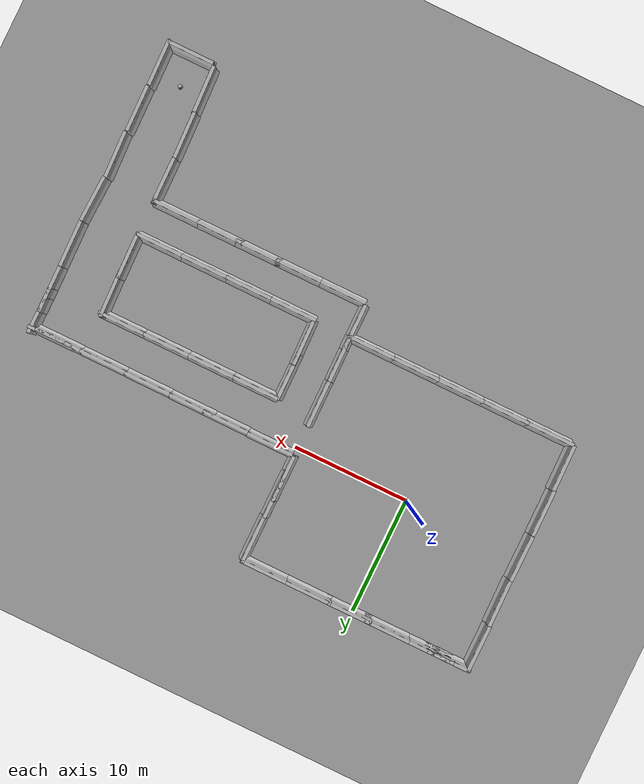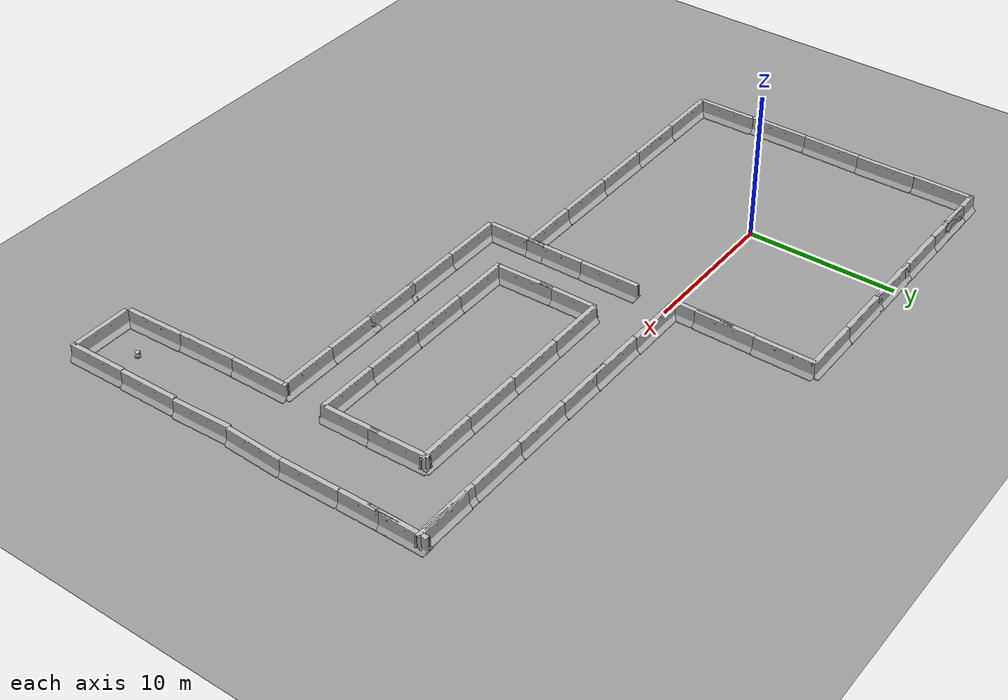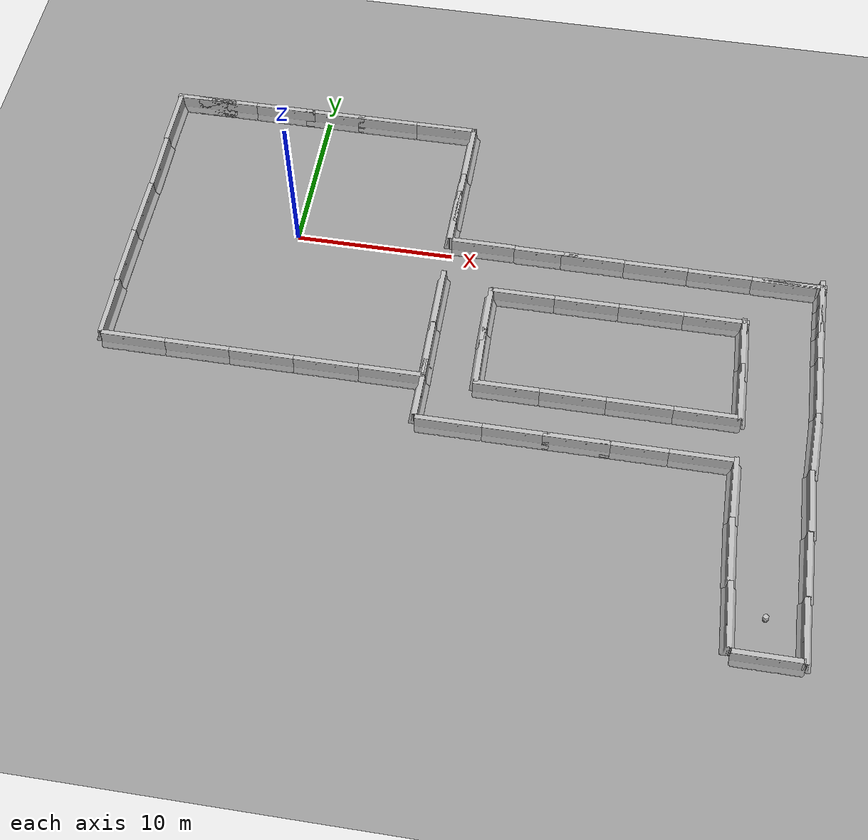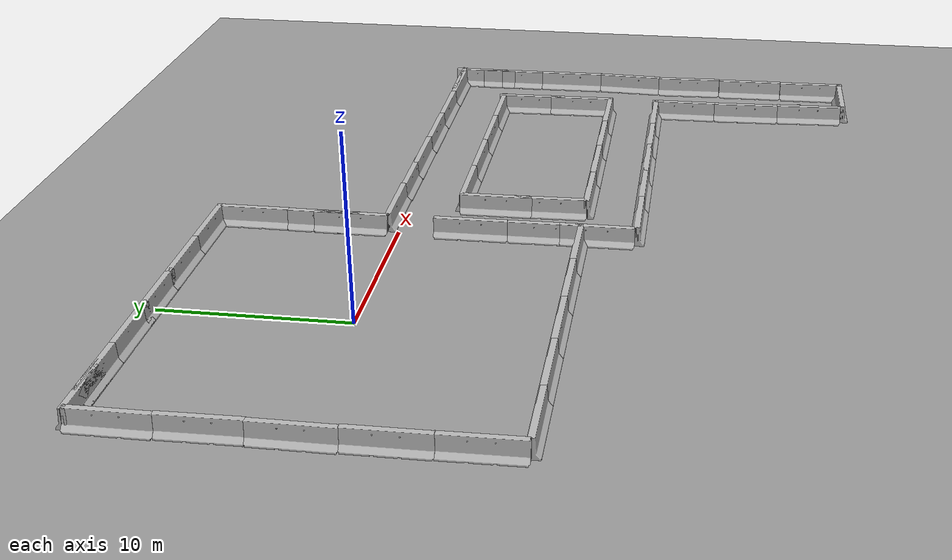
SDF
<sdf version="1.4">
 <world name="default">
  <light name="sun" type="directional">
   <pose>0 0 10 0 -0 0</pose>
   <diffuse>0.8 0.8 0.8 1</diffuse>
   <specular>0.2 0.2 0.2 1</specular>
   <attenuation>
    <range>1000</range>
    <constant>0.9</constant>
    <linear>0.01</linear>
    <quadratic>0.001</quadratic>
   </attenuation>
   <direction>0.5 0.1 -0.9</direction>
  </light>
  <scene><ambient>0.4 0.4 0.4 1</ambient><background>0.7 0.7 0.7 1</background><shadows>1</shadows></scene>
  <physics type="ode">
   <max_step_size>0.01</max_step_size>
   <real_time_factor>1</real_time_factor>
   <real_time_update_rate>100</real_time_update_rate>
   <gravity>0 0 -9.8</gravity>
  </physics>
  <model name="jersey_barrier">
   <static>1</static>
   <link name="link">
    <visual name="visual">
     <geometry><mesh><uri>model://jersey_barrier/meshes/jersey_barrier.dae</uri></mesh></geometry>
    </visual>
    <collision name="upright">
     <pose>0 0 0.5715 0 -0 0</pose>
     <geometry><box><size>4.06542 0.3063 1.143</size></box></geometry>
    </collision>
    <collision name="base">
     <pose>0 0 0.032258 0 -0 0</pose>
     <geometry><box><size>4.06542 0.8107 0.064516</size></box></geometry>
    </collision>
    <collision name="base2">
     <pose>0 0 0.1 0 -0 0</pose>
     <geometry><box><size>4.06542 0.65 0.1</size></box></geometry>
    </collision>
    <collision name="base3">
     <pose>0 0 0.2 0 -0 0</pose>
     <geometry><box><size>4.06542 0.5 0.1</size></box></geometry>
    </collision>
    <collision name="left-angle">
     <pose>0 -0.224 0.2401 0.9 -0 0</pose>
     <geometry><box><size>4.06542 0.5 0.064516</size></box></geometry>
    </collision>
    <collision name="right-angle">
     <pose>0 0.224 0.2401 -0.9 0 0</pose>
     <geometry><box><size>4.06542 0.5 0.064516</size></box></geometry>
    </collision>
    <velocity_decay><linear>0</linear><angular>0</angular></velocity_decay>
   </link>
   <pose>-10.1123 -7.95933 0 0 0 -1.55782</pose>
  </model>
  <model name="ground_plane_0">
   <static>1</static>
   <link name="link">
    <collision name="collision">
     <geometry><plane><normal>0 0 1</normal><size>100 100</size></plane></geometry>
     <surface><friction><ode><mu>100</mu><mu2>50</mu2></ode></friction></surface>
    </collision>
    <visual name="visual">
     <cast_shadows>0</cast_shadows>
     <geometry><plane><normal>0 0 1</normal><size>100 100</size></plane></geometry>
     <material>
      <script><uri>file://media/materials/scripts/gazebo.material</uri><name>Gazebo/Grey</name></script>
     </material>
    </visual>
    <velocity_decay><linear>0</linear><angular>0</angular></velocity_decay>
   </link>
   <pose>0.497681 0 0 0 -0 0</pose>
  </model>
  <spherical_coordinates>
   <surface_model>EARTH_WGS84</surface_model>
   <latitude_deg>0</latitude_deg>
   <longitude_deg>0</longitude_deg>
   <elevation>0</elevation>
   <heading_deg>0</heading_deg>
  </spherical_coordinates>
  <model name="mobile_base">
   <link name="base_footprint">
    <inertial>
     <pose>-0.00263512 -4.10874e-05 0.129243 0 -0 0</pose>
     <mass>4.6973</mass>
     <inertia>
      <ixx>0.1365</ixx>
      <ixy>-2.51802e-05</ixy>
      <ixz>0.0108194</ixz>
      <iyy>0.132157</iyy>
      <iyz>4.89572e-05</iyz>
      <izz>0.0741648</izz>
     </inertia>
    </inertial>
    <collision name="base_footprint_collision_base_link">
     <pose>0 0 0.06969 0 -0 0</pose>
     <geometry><cylinder><length>0.10938</length><radius>0.178</radius></cylinder></geometry>
     <surface><friction><ode><mu>0.3</mu><mu2>0.3</mu2></ode></friction></surface>
    </collision>
    <collision name="base_footprint_collision_camera_link">
     <pose>-0.087 -0.0015 0.2972 0 -0 0</pose>
     <geometry><box><size>0.073 0.276 0.072</size></box></geometry>
    </collision>
    <collision name="base_footprint_collision_caster_back_link">
     <pose>-0.135 0 0.0192 -1.5708 0 0</pose>
     <geometry><cylinder><length>0.0176</length><radius>0.017</radius></cylinder></geometry>
     <surface>
      <contact><ode><kp>1e+06</kp><kd>100</kd><max_vel>1</max_vel><min_depth>0.001</min_depth></ode></contact>
      <friction><ode><mu>0</mu><mu2>0</mu2></ode></friction>
     </surface>
    </collision>
    <collision name="base_footprint_collision_caster_front_link">
     <pose>0.115 0 0.0172 -1.5708 0 0</pose>
     <geometry><cylinder><length>0.0176</length><radius>0.017</radius></cylinder></geometry>
     <surface>
      <contact><ode><kp>1e+06</kp><kd>100</kd><max_vel>1</max_vel><min_depth>0.001</min_depth></ode></contact>
      <friction><ode><mu>0</mu><mu2>0</mu2></ode></friction>
     </surface>
    </collision>
    <collision name="base_footprint_collision_mount_asus_xtion_pro_link">
     <pose>-0.1024 0 0.2822 0 -0 0</pose>
     <geometry><box><size>0.033 0.276 0.012</size></box></geometry>
    </collision>
    <collision name="base_footprint_collision_plate_bottom_link">
     <pose>0 0 0.1408 0 -0 0</pose>
     <geometry><cylinder><length>0.006</length><radius>0.17</radius></cylinder></geometry>
    </collision>
    <collision name="base_footprint_collision_plate_middle_link">
     <pose>0 0 0.1976 0 -0 0</pose>
     <geometry><cylinder><length>0.006</length><radius>0.17</radius></cylinder></geometry>
    </collision>
    <collision name="base_footprint_collision_plate_top_link">
     <pose>0 0 0.4068 0 -0 0</pose>
     <geometry><cylinder><length>0.006</length><radius>0.17</radius></cylinder></geometry>
    </collision>
    <collision name="base_footprint_collision_pole_bottom_0_link">
     <pose>0.12 0.082 0.113 0 -0 0</pose>
     <geometry><cylinder><length>0.0492</length><radius>0.006</radius></cylinder></geometry>
    </collision>
    <collision name="base_footprint_collision_pole_bottom_1_link">
     <pose>0.055 0.12 0.113 0 -0 0</pose>
     <geometry><cylinder><length>0.0492</length><radius>0.006</radius></cylinder></geometry>
    </collision>
    <collision name="base_footprint_collision_pole_bottom_2_link">
     <pose>-0.055 0.12 0.113 0 -0 0</pose>
     <geometry><cylinder><length>0.0492</length><radius>0.006</radius></cylinder></geometry>
    </collision>
    <collision name="base_footprint_collision_pole_bottom_3_link">
     <pose>0.12 -0.082 0.113 0 -0 0</pose>
     <geometry><cylinder><length>0.0492</length><radius>0.006</radius></cylinder></geometry>
    </collision>
    <collision name="base_footprint_collision_pole_bottom_4_link">
     <pose>0.055 -0.12 0.113 0 -0 0</pose>
     <geometry><cylinder><length>0.0492</length><radius>0.006</radius></cylinder></geometry>
    </collision>
    <collision name="base_footprint_collision_pole_bottom_5_link">
     <pose>-0.055 -0.12 0.113 0 -0 0</pose>
     <geometry><cylinder><length>0.0492</length><radius>0.006</radius></cylinder></geometry>
    </collision>
    <collision name="base_footprint_collision_pole_kinect_0_link">
     <pose>-0.1024 0.098 0.2474 0 -0 0</pose>
     <geometry><cylinder><length>0.0936</length><radius>0.006</radius></cylinder></geometry>
    </collision>
    <collision name="base_footprint_collision_pole_kinect_1_link">
     <pose>-0.1024 -0.098 0.2474 0 -0 0</pose>
     <geometry><cylinder><length>0.0936</length><radius>0.006</radius></cylinder></geometry>
    </collision>
    <collision name="base_footprint_collision_pole_middle_0_link">
     <pose>0.0381 0.1505 0.1742 0 -0 0</pose>
     <geometry><cylinder><length>0.0608</length><radius>0.006</radius></cylinder></geometry>
    </collision>
    <collision name="base_footprint_collision_pole_middle_1_link">
     <pose>0.0381 -0.1505 0.1742 0 -0 0</pose>
     <geometry><cylinder><length>0.0608</length><radius>0.006</radius></cylinder></geometry>
    </collision>
    <collision name="base_footprint_collision_pole_middle_2_link">
     <pose>-0.0381 0.1505 0.1742 0 -0 0</pose>
     <geometry><cylinder><length>0.0608</length><radius>0.006</radius></cylinder></geometry>
    </collision>
    <collision name="base_footprint_collision_pole_middle_3_link">
     <pose>-0.0381 -0.1505 0.1742 0 -0 0</pose>
     <geometry><cylinder><length>0.0608</length><radius>0.006</radius></cylinder></geometry>
    </collision>
    <collision name="base_footprint_collision_pole_top_0_link">
     <pose>0.0381 0.1505 0.3022 0 -0 0</pose>
     <geometry><cylinder><length>0.2032</length><radius>0.006</radius></cylinder></geometry>
    </collision>
    <collision name="base_footprint_collision_pole_top_1_link">
     <pose>0.0381 -0.1505 0.3022 0 -0 0</pose>
     <geometry><cylinder><length>0.2032</length><radius>0.006</radius></cylinder></geometry>
    </collision>
    <collision name="base_footprint_collision_pole_top_2_link">
     <pose>-0.0381 0.1505 0.3022 0 -0 0</pose>
     <geometry><cylinder><length>0.2032</length><radius>0.006</radius></cylinder></geometry>
    </collision>
    <collision name="base_footprint_collision_pole_top_3_link">
     <pose>-0.0381 -0.1505 0.3022 0 -0 0</pose>
     <geometry><cylinder><length>0.2032</length><radius>0.006</radius></cylinder></geometry>
    </collision>
    <visual name="base_footprint_visual_base_link">
     <pose>0.001 0 0.06219 0 -0 0</pose>
     <geometry>
      <mesh><scale>1 1 1</scale><uri>/opt/ros/indigo/share/kobuki_description/meshes/main_body.dae</uri></mesh>
     </geometry>
    </visual>
    <visual name="base_footprint_visual_camera_link">
     <pose>-0.102 0.002 0.3012 0 -0 0</pose>
     <geometry>
      <mesh>
       <scale>1 1 1</scale>
       <uri>/opt/ros/indigo/share/turtlebot_description/meshes/sensors/xtion_pro_camera.dae</uri>
      </mesh>
     </geometry>
    </visual>
    <visual name="base_footprint_visual_mount_asus_xtion_pro_link">
     <pose>-0.1024 0 0.2822 -1.5708 0 0</pose>
     <geometry>
      <mesh>
       <scale>1 1 1</scale>
       <uri>/opt/ros/indigo/share/turtlebot_description/meshes/sensors/xtion_pro_stack.dae</uri>
      </mesh>
     </geometry>
    </visual>
    <visual name="base_footprint_visual_plate_bottom_link">
     <pose>0.02364 0 0.1408 0 -0 0</pose>
     <geometry>
      <mesh>
       <scale>1 1 1</scale>
       <uri>/opt/ros/indigo/share/turtlebot_description/meshes/stacks/hexagons/plate_bottom.dae</uri>
      </mesh>
     </geometry>
    </visual>
    <visual name="base_footprint_visual_plate_middle_link">
     <pose>-0.01364 0 0.1976 0 -0 0</pose>
     <geometry>
      <mesh>
       <scale>1 1 1</scale>
       <uri>/opt/ros/indigo/share/turtlebot_description/meshes/stacks/hexagons/plate_middle.dae</uri>
      </mesh>
     </geometry>
    </visual>
    <visual name="base_footprint_visual_plate_top_link">
     <pose>-0.01364 0 0.4068 0 -0 0</pose>
     <geometry>
      <mesh>
       <scale>1 1 1</scale>
       <uri>/opt/ros/indigo/share/turtlebot_description/meshes/stacks/hexagons/plate_top.dae</uri>
      </mesh>
     </geometry>
    </visual>
    <visual name="base_footprint_visual_pole_bottom_0_link">
     <pose>0.12 0.082 0.113 0 -0 0</pose>
     <geometry>
      <mesh>
       <scale>1 1 1</scale>
       <uri>/opt/ros/indigo/share/turtlebot_description/meshes/stacks/hexagons/pole_bottom.dae</uri>
      </mesh>
     </geometry>
    </visual>
    <visual name="base_footprint_visual_pole_bottom_1_link">
     <pose>0.055 0.12 0.113 0 -0 0</pose>
     <geometry>
      <mesh>
       <scale>1 1 1</scale>
       <uri>/opt/ros/indigo/share/turtlebot_description/meshes/stacks/hexagons/pole_bottom.dae</uri>
      </mesh>
     </geometry>
    </visual>
    <visual name="base_footprint_visual_pole_bottom_2_link">
     <pose>-0.055 0.12 0.113 0 -0 0</pose>
     <geometry>
      <mesh>
       <scale>1 1 1</scale>
       <uri>/opt/ros/indigo/share/turtlebot_description/meshes/stacks/hexagons/pole_bottom.dae</uri>
      </mesh>
     </geometry>
    </visual>
    <visual name="base_footprint_visual_pole_bottom_3_link">
     <pose>0.12 -0.082 0.113 0 -0 0</pose>
     <geometry>
      <mesh>
       <scale>1 1 1</scale>
       <uri>/opt/ros/indigo/share/turtlebot_description/meshes/stacks/hexagons/pole_bottom.dae</uri>
      </mesh>
     </geometry>
    </visual>
    <visual name="base_footprint_visual_pole_bottom_4_link">
     <pose>0.055 -0.12 0.113 0 -0 0</pose>
     <geometry>
      <mesh>
       <scale>1 1 1</scale>
       <uri>/opt/ros/indigo/share/turtlebot_description/meshes/stacks/hexagons/pole_bottom.dae</uri>
      </mesh>
     </geometry>
    </visual>
    <visual name="base_footprint_visual_pole_bottom_5_link">
     <pose>-0.055 -0.12 0.113 0 -0 0</pose>
     <geometry>
      <mesh>
       <scale>1 1 1</scale>
       <uri>/opt/ros/indigo/share/turtlebot_description/meshes/stacks/hexagons/pole_bottom.dae</uri>
      </mesh>
     </geometry>
    </visual>
    <visual name="base_footprint_visual_pole_kinect_0_link">
     <pose>-0.1024 0.098 0.2374 0 -0 0</pose>
     <geometry>
      <mesh>
       <scale>1 1 1</scale>
       <uri>/opt/ros/indigo/share/turtlebot_description/meshes/sensors/sensor_pole.dae</uri>
      </mesh>
     </geometry>
    </visual>
    <visual name="base_footprint_visual_pole_kinect_1_link">
     <pose>-0.1024 -0.098 0.2374 0 -0 0</pose>
     <geometry>
      <mesh>
       <scale>1 1 1</scale>
       <uri>/opt/ros/indigo/share/turtlebot_description/meshes/sensors/sensor_pole.dae</uri>
      </mesh>
     </geometry>
    </visual>
    <visual name="base_footprint_visual_pole_middle_0_link">
     <pose>0.0381 0.1505 0.1742 3.14159 -2.06823e-13 3.14159</pose>
     <geometry>
      <mesh>
       <scale>1 1 1</scale>
       <uri>/opt/ros/indigo/share/turtlebot_description/meshes/stacks/hexagons/pole_middle.dae</uri>
      </mesh>
     </geometry>
    </visual>
    <visual name="base_footprint_visual_pole_middle_1_link">
     <pose>0.0381 -0.1505 0.1742 3.14159 -2.06823e-13 3.14159</pose>
     <geometry>
      <mesh>
       <scale>1 1 1</scale>
       <uri>/opt/ros/indigo/share/turtlebot_description/meshes/stacks/hexagons/pole_middle.dae</uri>
      </mesh>
     </geometry>
    </visual>
    <visual name="base_footprint_visual_pole_middle_2_link">
     <pose>-0.0381 0.1505 0.1742 3.14159 -2.06823e-13 3.14159</pose>
     <geometry>
      <mesh>
       <scale>1 1 1</scale>
       <uri>/opt/ros/indigo/share/turtlebot_description/meshes/stacks/hexagons/pole_middle.dae</uri>
      </mesh>
     </geometry>
    </visual>
    <visual name="base_footprint_visual_pole_middle_3_link">
     <pose>-0.0381 -0.1505 0.1742 3.14159 -2.06823e-13 3.14159</pose>
     <geometry>
      <mesh>
       <scale>1 1 1</scale>
       <uri>/opt/ros/indigo/share/turtlebot_description/meshes/stacks/hexagons/pole_middle.dae</uri>
      </mesh>
     </geometry>
    </visual>
    <visual name="base_footprint_visual_pole_top_0_link">
     <pose>0.0381 0.1505 0.3022 0 -0 0</pose>
     <geometry>
      <mesh>
       <scale>1 1 1</scale>
       <uri>/opt/ros/indigo/share/turtlebot_description/meshes/stacks/hexagons/pole_top.dae</uri>
      </mesh>
     </geometry>
    </visual>
    <visual name="base_footprint_visual_pole_top_1_link">
     <pose>0.0381 -0.1505 0.3022 0 -0 0</pose>
     <geometry>
      <mesh>
       <scale>1 1 1</scale>
       <uri>/opt/ros/indigo/share/turtlebot_description/meshes/stacks/hexagons/pole_top.dae</uri>
      </mesh>
     </geometry>
    </visual>
    <visual name="base_footprint_visual_pole_top_2_link">
     <pose>-0.0381 0.1505 0.3022 0 -0 0</pose>
     <geometry>
      <mesh>
       <scale>1 1 1</scale>
       <uri>/opt/ros/indigo/share/turtlebot_description/meshes/stacks/hexagons/pole_top.dae</uri>
      </mesh>
     </geometry>
    </visual>
    <visual name="base_footprint_visual_pole_top_3_link">
     <pose>-0.0381 -0.1505 0.3022 0 -0 0</pose>
     <geometry>
      <mesh>
       <scale>1 1 1</scale>
       <uri>/opt/ros/indigo/share/turtlebot_description/meshes/stacks/hexagons/pole_top.dae</uri>
      </mesh>
     </geometry>
    </visual>
    <velocity_decay><linear>0</linear><angular>0</angular></velocity_decay>
    <sensor name="bumpers" type="contact">
     <always_on>1</always_on>
     <update_rate>50</update_rate>
     <visualize>1</visualize>
     <contact><collision>base_footprint_collision_base_link</collision><topic>__default_topic__</topic></contact>
     <pose>0 0 0.0102 0 -0 0</pose>
    </sensor>
    <velocity_decay><linear>0</linear><angular>0</angular></velocity_decay>
    <sensor name="camera" type="depth">
     <always_on>1</always_on>
     <update_rate>20</update_rate>
     <camera name="__default__">
      <horizontal_fov>1.0472</horizontal_fov>
      <image><format>B8G8R8</format><width>640</width><height>480</height></image>
      <clip><near>0.05</near><far>8</far></clip>
     </camera>
     <plugin name="kinect_camera_controller" filename="libgazebo_ros_openni_kinect.so">
      <cameraName>camera</cameraName>
      <alwaysOn>true</alwaysOn>
      <updateRate>10</updateRate>
      <imageTopicName>rgb/image_raw</imageTopicName>
      <depthImageTopicName>depth/image_raw</depthImageTopicName>
      <pointCloudTopicName>depth/points</pointCloudTopicName>
      <cameraInfoTopicName>rgb/camera_info</cameraInfoTopicName>
      <depthImageCameraInfoTopicName>depth/camera_info</depthImageCameraInfoTopicName>
      <frameName>camera_depth_optical_frame</frameName>
      <baseline>0.1</baseline>
      <distortion_k1>0.0</distortion_k1>
      <distortion_k2>0.0</distortion_k2>
      <distortion_k3>0.0</distortion_k3>
      <distortion_t1>0.0</distortion_t1>
      <distortion_t2>0.0</distortion_t2>
      <pointCloudCutoff>0.4</pointCloudCutoff>
      <robotNamespace>/</robotNamespace>
     </plugin>
     <pose>-0.087 -0.0015 0.2972 0 -0 0</pose>
    </sensor>
    <velocity_decay><linear>0</linear><angular>0</angular></velocity_decay>
    <velocity_decay><linear>0</linear><angular>0</angular></velocity_decay>
    <velocity_decay><linear>0</linear><angular>0</angular></velocity_decay>
    <sensor name="cliff_sensor_front" type="ray">
     <always_on>1</always_on>
     <update_rate>50</update_rate>
     <visualize>1</visualize>
     <ray>
      <scan>
       <horizontal>
        <samples>50</samples>
        <resolution>1</resolution>
        <min_angle>-0.0436</min_angle>
        <max_angle>0.0436</max_angle>
       </horizontal>
      </scan>
      <range><min>0.01</min><max>0.15</max><resolution>1</resolution></range>
     </ray>
     <pose>0.156 0 0.0316 3.14159 1.57079 3.14159</pose>
    </sensor>
    <velocity_decay><linear>0</linear><angular>0</angular></velocity_decay>
    <sensor name="cliff_sensor_left" type="ray">
     <always_on>1</always_on>
     <update_rate>50</update_rate>
     <visualize>1</visualize>
     <ray>
      <scan>
       <horizontal>
        <samples>50</samples>
        <resolution>1</resolution>
        <min_angle>-0.0436</min_angle>
        <max_angle>0.0436</max_angle>
       </horizontal>
      </scan>
      <range><min>0.01</min><max>0.15</max><resolution>1</resolution></range>
     </ray>
     <pose>0.08734 0.13601 0.0316 3.14159 1.57079 3.14159</pose>
    </sensor>
    <velocity_decay><linear>0</linear><angular>0</angular></velocity_decay>
    <sensor name="cliff_sensor_right" type="ray">
     <always_on>1</always_on>
     <update_rate>50</update_rate>
     <visualize>1</visualize>
     <ray>
      <scan>
       <horizontal>
        <samples>50</samples>
        <resolution>1</resolution>
        <min_angle>-0.0436</min_angle>
        <max_angle>0.0436</max_angle>
       </horizontal>
      </scan>
      <range><min>0.01</min><max>0.15</max><resolution>1</resolution></range>
     </ray>
     <pose>0.085 -0.13601 0.0316 3.14159 1.57079 3.14159</pose>
    </sensor>
    <velocity_decay><linear>0</linear><angular>0</angular></velocity_decay>
    <sensor name="imu" type="imu">
     <always_on>1</always_on>
     <update_rate>50</update_rate>
     <visualize>0</visualize>
     <imu>
      <noise>
       <type>gaussian</type>
       <rate><mean>0</mean><stddev>1.96e-06</stddev><bias_mean>0</bias_mean><bias_stddev>0</bias_stddev></rate>
       <accel><mean>0</mean><stddev>0.017</stddev><bias_mean>0.1</bias_mean><bias_stddev>0.001</bias_stddev></accel>
      </noise>
     </imu>
     <pose>0.056 0.062 0.0304 0 -0 0</pose>
    </sensor>
   </link>
   <link name="wheel_left_link">
    <pose>0 0.115 0.0352 -1.5708 0 0</pose>
    <inertial>
     <mass>0.01</mass>
     <inertia><ixx>0.001</ixx><ixy>0</ixy><ixz>0</ixz><iyy>0.001</iyy><iyz>0</iyz><izz>0.001</izz></inertia>
    </inertial>
    <collision name="wheel_left_link_collision">
     <geometry><cylinder><length>0.0206</length><radius>0.0352</radius></cylinder></geometry>
     <surface>
      <contact><ode><kp>1e+06</kp><kd>100</kd><max_vel>1</max_vel><min_depth>0.001</min_depth></ode></contact>
      <friction><ode><mu>1</mu><mu2>1</mu2></ode></friction>
     </surface>
    </collision>
    <visual name="wheel_left_link_visual">
     <geometry>
      <mesh><scale>1 1 1</scale><uri>/opt/ros/indigo/share/kobuki_description/meshes/wheel.dae</uri></mesh>
     </geometry>
    </visual>
    <velocity_decay><linear>0</linear><angular>0</angular></velocity_decay>
   </link>
   <joint name="wheel_left_joint" type="revolute">
    <child>wheel_left_link</child>
    <parent>base_footprint</parent>
    <axis><xyz>0 1 0</xyz><limit><lower>-1e+16</lower><upper>1e+16</upper></limit></axis>
   </joint>
   <link name="wheel_right_link">
    <pose>0 -0.115 0.0352 -1.5708 0 0</pose>
    <inertial>
     <mass>0.01</mass>
     <inertia><ixx>0.001</ixx><ixy>0</ixy><ixz>0</ixz><iyy>0.001</iyy><iyz>0</iyz><izz>0.001</izz></inertia>
    </inertial>
    <collision name="wheel_right_link_collision">
     <geometry><cylinder><length>0.0206</length><radius>0.035</radius></cylinder></geometry>
     <surface>
      <contact><ode><kp>1e+06</kp><kd>100</kd><max_vel>1</max_vel><min_depth>0.001</min_depth></ode></contact>
      <friction><ode><mu>1</mu><mu2>1</mu2></ode></friction>
     </surface>
    </collision>
    <visual name="wheel_right_link_visual">
     <geometry>
      <mesh><scale>1 1 1</scale><uri>/opt/ros/indigo/share/kobuki_description/meshes/wheel.dae</uri></mesh>
     </geometry>
    </visual>
    <velocity_decay><linear>0</linear><angular>0</angular></velocity_decay>
   </link>
   <joint name="wheel_right_joint" type="revolute">
    <child>wheel_right_link</child>
    <parent>base_footprint</parent>
    <axis><xyz>0 1 0</xyz><limit><lower>-1e+16</lower><upper>1e+16</upper></limit></axis>
   </joint>
   <static>0</static>
   <plugin name="kobuki_controller" filename="libgazebo_ros_kobuki.so">
    <publish_tf>1</publish_tf>
    <left_wheel_joint_name>wheel_left_joint</left_wheel_joint_name>
    <right_wheel_joint_name>wheel_right_joint</right_wheel_joint_name>
    <wheel_separation>.230</wheel_separation>
    <wheel_diameter>0.070</wheel_diameter>
    <torque>1.0</torque>
    <velocity_command_timeout>0.6</velocity_command_timeout>
    <cliff_sensor_left_name>cliff_sensor_left</cliff_sensor_left_name>
    <cliff_sensor_center_name>cliff_sensor_front</cliff_sensor_center_name>
    <cliff_sensor_right_name>cliff_sensor_right</cliff_sensor_right_name>
    <cliff_detection_threshold>0.04</cliff_detection_threshold>
    <bumper_name>bumpers</bumper_name>
    <imu_name>imu</imu_name>
    <robotNamespace>/</robotNamespace>
   </plugin>
   <pose>31.2241 -22.3365 -0.001131 6e-05 -0.007997 -1.09406</pose>
  </model>
  <model name="jersey_barrier_0">
   <static>1</static>
   <link name="link">
    <visual name="visual">
     <geometry><mesh><uri>model://jersey_barrier/meshes/jersey_barrier.dae</uri></mesh></geometry>
    </visual>
    <collision name="upright">
     <pose>0 0 0.5715 0 -0 0</pose>
     <geometry><box><size>4.06542 0.3063 1.143</size></box></geometry>
    </collision>
    <collision name="base">
     <pose>0 0 0.032258 0 -0 0</pose>
     <geometry><box><size>4.06542 0.8107 0.064516</size></box></geometry>
    </collision>
    <collision name="base2">
     <pose>0 0 0.1 0 -0 0</pose>
     <geometry><box><size>4.06542 0.65 0.1</size></box></geometry>
    </collision>
    <collision name="base3">
     <pose>0 0 0.2 0 -0 0</pose>
     <geometry><box><size>4.06542 0.5 0.1</size></box></geometry>
    </collision>
    <collision name="left-angle">
     <pose>0 -0.224 0.2401 0.9 -0 0</pose>
     <geometry><box><size>4.06542 0.5 0.064516</size></box></geometry>
    </collision>
    <collision name="right-angle">
     <pose>0 0.224 0.2401 -0.9 0 0</pose>
     <geometry><box><size>4.06542 0.5 0.064516</size></box></geometry>
    </collision>
    <velocity_decay><linear>0</linear><angular>0</angular></velocity_decay>
   </link>
   <pose>-10.2064 -3.99 0.02669 0 0 -1.56734</pose>
  </model>
  <model name="jersey_barrier_1">
   <static>1</static>
   <link name="link">
    <visual name="visual">
     <geometry><mesh><uri>model://jersey_barrier/meshes/jersey_barrier.dae</uri></mesh></geometry>
    </visual>
    <collision name="upright">
     <pose>0 0 0.5715 0 -0 0</pose>
     <geometry><box><size>4.06542 0.3063 1.143</size></box></geometry>
    </collision>
    <collision name="base">
     <pose>0 0 0.032258 0 -0 0</pose>
     <geometry><box><size>4.06542 0.8107 0.064516</size></box></geometry>
    </collision>
    <collision name="base2">
     <pose>0 0 0.1 0 -0 0</pose>
     <geometry><box><size>4.06542 0.65 0.1</size></box></geometry>
    </collision>
    <collision name="base3">
     <pose>0 0 0.2 0 -0 0</pose>
     <geometry><box><size>4.06542 0.5 0.1</size></box></geometry>
    </collision>
    <collision name="left-angle">
     <pose>0 -0.224 0.2401 0.9 -0 0</pose>
     <geometry><box><size>4.06542 0.5 0.064516</size></box></geometry>
    </collision>
    <collision name="right-angle">
     <pose>0 0.224 0.2401 -0.9 0 0</pose>
     <geometry><box><size>4.06542 0.5 0.064516</size></box></geometry>
    </collision>
    <velocity_decay><linear>0</linear><angular>0</angular></velocity_decay>
   </link>
   <pose>-10.2248 0.051346 0 0 0 -1.57545</pose>
  </model>
  <model name="jersey_barrier_2">
   <static>1</static>
   <link name="link">
    <visual name="visual">
     <geometry><mesh><uri>model://jersey_barrier/meshes/jersey_barrier.dae</uri></mesh></geometry>
    </visual>
    <collision name="upright">
     <pose>0 0 0.5715 0 -0 0</pose>
     <geometry><box><size>4.06542 0.3063 1.143</size></box></geometry>
    </collision>
    <collision name="base">
     <pose>0 0 0.032258 0 -0 0</pose>
     <geometry><box><size>4.06542 0.8107 0.064516</size></box></geometry>
    </collision>
    <collision name="base2">
     <pose>0 0 0.1 0 -0 0</pose>
     <geometry><box><size>4.06542 0.65 0.1</size></box></geometry>
    </collision>
    <collision name="base3">
     <pose>0 0 0.2 0 -0 0</pose>
     <geometry><box><size>4.06542 0.5 0.1</size></box></geometry>
    </collision>
    <collision name="left-angle">
     <pose>0 -0.224 0.2401 0.9 -0 0</pose>
     <geometry><box><size>4.06542 0.5 0.064516</size></box></geometry>
    </collision>
    <collision name="right-angle">
     <pose>0 0.224 0.2401 -0.9 0 0</pose>
     <geometry><box><size>4.06542 0.5 0.064516</size></box></geometry>
    </collision>
    <velocity_decay><linear>0</linear><angular>0</angular></velocity_decay>
   </link>
   <pose>-10.2081 4.04852 0 0 0 -1.55769</pose>
  </model>
  <model name="jersey_barrier_3">
   <static>1</static>
   <link name="link">
    <visual name="visual">
     <geometry><mesh><uri>model://jersey_barrier/meshes/jersey_barrier.dae</uri></mesh></geometry>
    </visual>
    <collision name="upright">
     <pose>0 0 0.5715 0 -0 0</pose>
     <geometry><box><size>4.06542 0.3063 1.143</size></box></geometry>
    </collision>
    <collision name="base">
     <pose>0 0 0.032258 0 -0 0</pose>
     <geometry><box><size>4.06542 0.8107 0.064516</size></box></geometry>
    </collision>
    <collision name="base2">
     <pose>0 0 0.1 0 -0 0</pose>
     <geometry><box><size>4.06542 0.65 0.1</size></box></geometry>
    </collision>
    <collision name="base3">
     <pose>0 0 0.2 0 -0 0</pose>
     <geometry><box><size>4.06542 0.5 0.1</size></box></geometry>
    </collision>
    <collision name="left-angle">
     <pose>0 -0.224 0.2401 0.9 -0 0</pose>
     <geometry><box><size>4.06542 0.5 0.064516</size></box></geometry>
    </collision>
    <collision name="right-angle">
     <pose>0 0.224 0.2401 -0.9 0 0</pose>
     <geometry><box><size>4.06542 0.5 0.064516</size></box></geometry>
    </collision>
    <velocity_decay><linear>0</linear><angular>0</angular></velocity_decay>
   </link>
   <pose>-10.2743 8.06249 0 0 -0 1.56778</pose>
  </model>
  <model name="jersey_barrier_4">
   <static>1</static>
   <link name="link">
    <visual name="visual">
     <geometry><mesh><uri>model://jersey_barrier/meshes/jersey_barrier.dae</uri></mesh></geometry>
    </visual>
    <collision name="upright">
     <pose>0 0 0.5715 0 -0 0</pose>
     <geometry><box><size>4.06542 0.3063 1.143</size></box></geometry>
    </collision>
    <collision name="base">
     <pose>0 0 0.032258 0 -0 0</pose>
     <geometry><box><size>4.06542 0.8107 0.064516</size></box></geometry>
    </collision>
    <collision name="base2">
     <pose>0 0 0.1 0 -0 0</pose>
     <geometry><box><size>4.06542 0.65 0.1</size></box></geometry>
    </collision>
    <collision name="base3">
     <pose>0 0 0.2 0 -0 0</pose>
     <geometry><box><size>4.06542 0.5 0.1</size></box></geometry>
    </collision>
    <collision name="left-angle">
     <pose>0 -0.224 0.2401 0.9 -0 0</pose>
     <geometry><box><size>4.06542 0.5 0.064516</size></box></geometry>
    </collision>
    <collision name="right-angle">
     <pose>0 0.224 0.2401 -0.9 0 0</pose>
     <geometry><box><size>4.06542 0.5 0.064516</size></box></geometry>
    </collision>
    <velocity_decay><linear>0</linear><angular>0</angular></velocity_decay>
   </link>
   <pose>-8 -10 0 0 -0 0</pose>
  </model>
  <model name="jersey_barrier_5">
   <static>1</static>
   <link name="link">
    <visual name="visual">
     <geometry><mesh><uri>model://jersey_barrier/meshes/jersey_barrier.dae</uri></mesh></geometry>
    </visual>
    <collision name="upright">
     <pose>0 0 0.5715 0 -0 0</pose>
     <geometry><box><size>4.06542 0.3063 1.143</size></box></geometry>
    </collision>
    <collision name="base">
     <pose>0 0 0.032258 0 -0 0</pose>
     <geometry><box><size>4.06542 0.8107 0.064516</size></box></geometry>
    </collision>
    <collision name="base2">
     <pose>0 0 0.1 0 -0 0</pose>
     <geometry><box><size>4.06542 0.65 0.1</size></box></geometry>
    </collision>
    <collision name="base3">
     <pose>0 0 0.2 0 -0 0</pose>
     <geometry><box><size>4.06542 0.5 0.1</size></box></geometry>
    </collision>
    <collision name="left-angle">
     <pose>0 -0.224 0.2401 0.9 -0 0</pose>
     <geometry><box><size>4.06542 0.5 0.064516</size></box></geometry>
    </collision>
    <collision name="right-angle">
     <pose>0 0.224 0.2401 -0.9 0 0</pose>
     <geometry><box><size>4.06542 0.5 0.064516</size></box></geometry>
    </collision>
    <velocity_decay><linear>0</linear><angular>0</angular></velocity_decay>
   </link>
   <pose>-4 -10 0 0 -0 0</pose>
  </model>
  <model name="jersey_barrier_6">
   <static>1</static>
   <link name="link">
    <visual name="visual">
     <geometry><mesh><uri>model://jersey_barrier/meshes/jersey_barrier.dae</uri></mesh></geometry>
    </visual>
    <collision name="upright">
     <pose>0 0 0.5715 0 -0 0</pose>
     <geometry><box><size>4.06542 0.3063 1.143</size></box></geometry>
    </collision>
    <collision name="base">
     <pose>0 0 0.032258 0 -0 0</pose>
     <geometry><box><size>4.06542 0.8107 0.064516</size></box></geometry>
    </collision>
    <collision name="base2">
     <pose>0 0 0.1 0 -0 0</pose>
     <geometry><box><size>4.06542 0.65 0.1</size></box></geometry>
    </collision>
    <collision name="base3">
     <pose>0 0 0.2 0 -0 0</pose>
     <geometry><box><size>4.06542 0.5 0.1</size></box></geometry>
    </collision>
    <collision name="left-angle">
     <pose>0 -0.224 0.2401 0.9 -0 0</pose>
     <geometry><box><size>4.06542 0.5 0.064516</size></box></geometry>
    </collision>
    <collision name="right-angle">
     <pose>0 0.224 0.2401 -0.9 0 0</pose>
     <geometry><box><size>4.06542 0.5 0.064516</size></box></geometry>
    </collision>
    <velocity_decay><linear>0</linear><angular>0</angular></velocity_decay>
   </link>
   <pose>0 -10 0 0 -0 0</pose>
  </model>
  <model name="jersey_barrier_7">
   <static>1</static>
   <link name="link">
    <visual name="visual">
     <geometry><mesh><uri>model://jersey_barrier/meshes/jersey_barrier.dae</uri></mesh></geometry>
    </visual>
    <collision name="upright">
     <pose>0 0 0.5715 0 -0 0</pose>
     <geometry><box><size>4.06542 0.3063 1.143</size></box></geometry>
    </collision>
    <collision name="base">
     <pose>0 0 0.032258 0 -0 0</pose>
     <geometry><box><size>4.06542 0.8107 0.064516</size></box></geometry>
    </collision>
    <collision name="base2">
     <pose>0 0 0.1 0 -0 0</pose>
     <geometry><box><size>4.06542 0.65 0.1</size></box></geometry>
    </collision>
    <collision name="base3">
     <pose>0 0 0.2 0 -0 0</pose>
     <geometry><box><size>4.06542 0.5 0.1</size></box></geometry>
    </collision>
    <collision name="left-angle">
     <pose>0 -0.224 0.2401 0.9 -0 0</pose>
     <geometry><box><size>4.06542 0.5 0.064516</size></box></geometry>
    </collision>
    <collision name="right-angle">
     <pose>0 0.224 0.2401 -0.9 0 0</pose>
     <geometry><box><size>4.06542 0.5 0.064516</size></box></geometry>
    </collision>
    <velocity_decay><linear>0</linear><angular>0</angular></velocity_decay>
   </link>
   <pose>4 -10 0 0 -0 0</pose>
  </model>
  <model name="jersey_barrier_8">
   <static>1</static>
   <link name="link">
    <visual name="visual">
     <geometry><mesh><uri>model://jersey_barrier/meshes/jersey_barrier.dae</uri></mesh></geometry>
    </visual>
    <collision name="upright">
     <pose>0 0 0.5715 0 -0 0</pose>
     <geometry><box><size>4.06542 0.3063 1.143</size></box></geometry>
    </collision>
    <collision name="base">
     <pose>0 0 0.032258 0 -0 0</pose>
     <geometry><box><size>4.06542 0.8107 0.064516</size></box></geometry>
    </collision>
    <collision name="base2">
     <pose>0 0 0.1 0 -0 0</pose>
     <geometry><box><size>4.06542 0.65 0.1</size></box></geometry>
    </collision>
    <collision name="base3">
     <pose>0 0 0.2 0 -0 0</pose>
     <geometry><box><size>4.06542 0.5 0.1</size></box></geometry>
    </collision>
    <collision name="left-angle">
     <pose>0 -0.224 0.2401 0.9 -0 0</pose>
     <geometry><box><size>4.06542 0.5 0.064516</size></box></geometry>
    </collision>
    <collision name="right-angle">
     <pose>0 0.224 0.2401 -0.9 0 0</pose>
     <geometry><box><size>4.06542 0.5 0.064516</size></box></geometry>
    </collision>
    <velocity_decay><linear>0</linear><angular>0</angular></velocity_decay>
   </link>
   <pose>8 -10 0 0 -0 0</pose>
  </model>
  <model name="jersey_barrier_9">
   <static>1</static>
   <link name="link">
    <visual name="visual">
     <geometry><mesh><uri>model://jersey_barrier/meshes/jersey_barrier.dae</uri></mesh></geometry>
    </visual>
    <collision name="upright">
     <pose>0 0 0.5715 0 -0 0</pose>
     <geometry><box><size>4.06542 0.3063 1.143</size></box></geometry>
    </collision>
    <collision name="base">
     <pose>0 0 0.032258 0 -0 0</pose>
     <geometry><box><size>4.06542 0.8107 0.064516</size></box></geometry>
    </collision>
    <collision name="base2">
     <pose>0 0 0.1 0 -0 0</pose>
     <geometry><box><size>4.06542 0.65 0.1</size></box></geometry>
    </collision>
    <collision name="base3">
     <pose>0 0 0.2 0 -0 0</pose>
     <geometry><box><size>4.06542 0.5 0.1</size></box></geometry>
    </collision>
    <collision name="left-angle">
     <pose>0 -0.224 0.2401 0.9 -0 0</pose>
     <geometry><box><size>4.06542 0.5 0.064516</size></box></geometry>
    </collision>
    <collision name="right-angle">
     <pose>0 0.224 0.2401 -0.9 0 0</pose>
     <geometry><box><size>4.06542 0.5 0.064516</size></box></geometry>
    </collision>
    <velocity_decay><linear>0</linear><angular>0</angular></velocity_decay>
   </link>
   <pose>9.92231 -8.06434 0 0 0 -1.55766</pose>
  </model>
  <model name="jersey_barrier_10">
   <static>1</static>
   <link name="link">
    <visual name="visual">
     <geometry><mesh><uri>model://jersey_barrier/meshes/jersey_barrier.dae</uri></mesh></geometry>
    </visual>
    <collision name="upright">
     <pose>0 0 0.5715 0 -0 0</pose>
     <geometry><box><size>4.06542 0.3063 1.143</size></box></geometry>
    </collision>
    <collision name="base">
     <pose>0 0 0.032258 0 -0 0</pose>
     <geometry><box><size>4.06542 0.8107 0.064516</size></box></geometry>
    </collision>
    <collision name="base2">
     <pose>0 0 0.1 0 -0 0</pose>
     <geometry><box><size>4.06542 0.65 0.1</size></box></geometry>
    </collision>
    <collision name="base3">
     <pose>0 0 0.2 0 -0 0</pose>
     <geometry><box><size>4.06542 0.5 0.1</size></box></geometry>
    </collision>
    <collision name="left-angle">
     <pose>0 -0.224 0.2401 0.9 -0 0</pose>
     <geometry><box><size>4.06542 0.5 0.064516</size></box></geometry>
    </collision>
    <collision name="right-angle">
     <pose>0 0.224 0.2401 -0.9 0 0</pose>
     <geometry><box><size>4.06542 0.5 0.064516</size></box></geometry>
    </collision>
    <velocity_decay><linear>0</linear><angular>0</angular></velocity_decay>
   </link>
   <pose>9.88698 -4.02592 0 0 -0 1.57868</pose>
  </model>
  <model name="jersey_barrier_11">
   <static>1</static>
   <link name="link">
    <visual name="visual">
     <geometry><mesh><uri>model://jersey_barrier/meshes/jersey_barrier.dae</uri></mesh></geometry>
    </visual>
    <collision name="upright">
     <pose>0 0 0.5715 0 -0 0</pose>
     <geometry><box><size>4.06542 0.3063 1.143</size></box></geometry>
    </collision>
    <collision name="base">
     <pose>0 0 0.032258 0 -0 0</pose>
     <geometry><box><size>4.06542 0.8107 0.064516</size></box></geometry>
    </collision>
    <collision name="base2">
     <pose>0 0 0.1 0 -0 0</pose>
     <geometry><box><size>4.06542 0.65 0.1</size></box></geometry>
    </collision>
    <collision name="base3">
     <pose>0 0 0.2 0 -0 0</pose>
     <geometry><box><size>4.06542 0.5 0.1</size></box></geometry>
    </collision>
    <collision name="left-angle">
     <pose>0 -0.224 0.2401 0.9 -0 0</pose>
     <geometry><box><size>4.06542 0.5 0.064516</size></box></geometry>
    </collision>
    <collision name="right-angle">
     <pose>0 0.224 0.2401 -0.9 0 0</pose>
     <geometry><box><size>4.06542 0.5 0.064516</size></box></geometry>
    </collision>
    <velocity_decay><linear>0</linear><angular>0</angular></velocity_decay>
   </link>
   <pose>9.81563 2.6045 0 0 0 -1.57159</pose>
  </model>
  <model name="jersey_barrier_12">
   <static>1</static>
   <link name="link">
    <visual name="visual">
     <geometry><mesh><uri>model://jersey_barrier/meshes/jersey_barrier.dae</uri></mesh></geometry>
    </visual>
    <collision name="upright">
     <pose>0 0 0.5715 0 -0 0</pose>
     <geometry><box><size>4.06542 0.3063 1.143</size></box></geometry>
    </collision>
    <collision name="base">
     <pose>0 0 0.032258 0 -0 0</pose>
     <geometry><box><size>4.06542 0.8107 0.064516</size></box></geometry>
    </collision>
    <collision name="base2">
     <pose>0 0 0.1 0 -0 0</pose>
     <geometry><box><size>4.06542 0.65 0.1</size></box></geometry>
    </collision>
    <collision name="base3">
     <pose>0 0 0.2 0 -0 0</pose>
     <geometry><box><size>4.06542 0.5 0.1</size></box></geometry>
    </collision>
    <collision name="left-angle">
     <pose>0 -0.224 0.2401 0.9 -0 0</pose>
     <geometry><box><size>4.06542 0.5 0.064516</size></box></geometry>
    </collision>
    <collision name="right-angle">
     <pose>0 0.224 0.2401 -0.9 0 0</pose>
     <geometry><box><size>4.06542 0.5 0.064516</size></box></geometry>
    </collision>
    <velocity_decay><linear>0</linear><angular>0</angular></velocity_decay>
   </link>
   <pose>9.8385 4.09189 0 0 0 -1.57013</pose>
  </model>
  <model name="jersey_barrier_13">
   <static>1</static>
   <link name="link">
    <visual name="visual">
     <geometry><mesh><uri>model://jersey_barrier/meshes/jersey_barrier.dae</uri></mesh></geometry>
    </visual>
    <collision name="upright">
     <pose>0 0 0.5715 0 -0 0</pose>
     <geometry><box><size>4.06542 0.3063 1.143</size></box></geometry>
    </collision>
    <collision name="base">
     <pose>0 0 0.032258 0 -0 0</pose>
     <geometry><box><size>4.06542 0.8107 0.064516</size></box></geometry>
    </collision>
    <collision name="base2">
     <pose>0 0 0.1 0 -0 0</pose>
     <geometry><box><size>4.06542 0.65 0.1</size></box></geometry>
    </collision>
    <collision name="base3">
     <pose>0 0 0.2 0 -0 0</pose>
     <geometry><box><size>4.06542 0.5 0.1</size></box></geometry>
    </collision>
    <collision name="left-angle">
     <pose>0 -0.224 0.2401 0.9 -0 0</pose>
     <geometry><box><size>4.06542 0.5 0.064516</size></box></geometry>
    </collision>
    <collision name="right-angle">
     <pose>0 0.224 0.2401 -0.9 0 0</pose>
     <geometry><box><size>4.06542 0.5 0.064516</size></box></geometry>
    </collision>
    <velocity_decay><linear>0</linear><angular>0</angular></velocity_decay>
   </link>
   <pose>9.86951 8.08601 0 0 0 -1.56907</pose>
  </model>
  <model name="jersey_barrier_14">
   <static>1</static>
   <link name="link">
    <visual name="visual">
     <geometry><mesh><uri>model://jersey_barrier/meshes/jersey_barrier.dae</uri></mesh></geometry>
    </visual>
    <collision name="upright">
     <pose>0 0 0.5715 0 -0 0</pose>
     <geometry><box><size>4.06542 0.3063 1.143</size></box></geometry>
    </collision>
    <collision name="base">
     <pose>0 0 0.032258 0 -0 0</pose>
     <geometry><box><size>4.06542 0.8107 0.064516</size></box></geometry>
    </collision>
    <collision name="base2">
     <pose>0 0 0.1 0 -0 0</pose>
     <geometry><box><size>4.06542 0.65 0.1</size></box></geometry>
    </collision>
    <collision name="base3">
     <pose>0 0 0.2 0 -0 0</pose>
     <geometry><box><size>4.06542 0.5 0.1</size></box></geometry>
    </collision>
    <collision name="left-angle">
     <pose>0 -0.224 0.2401 0.9 -0 0</pose>
     <geometry><box><size>4.06542 0.5 0.064516</size></box></geometry>
    </collision>
    <collision name="right-angle">
     <pose>0 0.224 0.2401 -0.9 0 0</pose>
     <geometry><box><size>4.06542 0.5 0.064516</size></box></geometry>
    </collision>
    <velocity_decay><linear>0</linear><angular>0</angular></velocity_decay>
   </link>
   <pose>8 10 0 0 -0 0</pose>
  </model>
  <model name="jersey_barrier_15">
   <static>1</static>
   <link name="link">
    <visual name="visual">
     <geometry><mesh><uri>model://jersey_barrier/meshes/jersey_barrier.dae</uri></mesh></geometry>
    </visual>
    <collision name="upright">
     <pose>0 0 0.5715 0 -0 0</pose>
     <geometry><box><size>4.06542 0.3063 1.143</size></box></geometry>
    </collision>
    <collision name="base">
     <pose>0 0 0.032258 0 -0 0</pose>
     <geometry><box><size>4.06542 0.8107 0.064516</size></box></geometry>
    </collision>
    <collision name="base2">
     <pose>0 0 0.1 0 -0 0</pose>
     <geometry><box><size>4.06542 0.65 0.1</size></box></geometry>
    </collision>
    <collision name="base3">
     <pose>0 0 0.2 0 -0 0</pose>
     <geometry><box><size>4.06542 0.5 0.1</size></box></geometry>
    </collision>
    <collision name="left-angle">
     <pose>0 -0.224 0.2401 0.9 -0 0</pose>
     <geometry><box><size>4.06542 0.5 0.064516</size></box></geometry>
    </collision>
    <collision name="right-angle">
     <pose>0 0.224 0.2401 -0.9 0 0</pose>
     <geometry><box><size>4.06542 0.5 0.064516</size></box></geometry>
    </collision>
    <velocity_decay><linear>0</linear><angular>0</angular></velocity_decay>
   </link>
   <pose>4 10 0 0 -0 0</pose>
  </model>
  <model name="jersey_barrier_16">
   <static>1</static>
   <link name="link">
    <visual name="visual">
     <geometry><mesh><uri>model://jersey_barrier/meshes/jersey_barrier.dae</uri></mesh></geometry>
    </visual>
    <collision name="upright">
     <pose>0 0 0.5715 0 -0 0</pose>
     <geometry><box><size>4.06542 0.3063 1.143</size></box></geometry>
    </collision>
    <collision name="base">
     <pose>0 0 0.032258 0 -0 0</pose>
     <geometry><box><size>4.06542 0.8107 0.064516</size></box></geometry>
    </collision>
    <collision name="base2">
     <pose>0 0 0.1 0 -0 0</pose>
     <geometry><box><size>4.06542 0.65 0.1</size></box></geometry>
    </collision>
    <collision name="base3">
     <pose>0 0 0.2 0 -0 0</pose>
     <geometry><box><size>4.06542 0.5 0.1</size></box></geometry>
    </collision>
    <collision name="left-angle">
     <pose>0 -0.224 0.2401 0.9 -0 0</pose>
     <geometry><box><size>4.06542 0.5 0.064516</size></box></geometry>
    </collision>
    <collision name="right-angle">
     <pose>0 0.224 0.2401 -0.9 0 0</pose>
     <geometry><box><size>4.06542 0.5 0.064516</size></box></geometry>
    </collision>
    <velocity_decay><linear>0</linear><angular>0</angular></velocity_decay>
   </link>
   <pose>0.403632 10 0 0 -0 0</pose>
  </model>
  <model name="jersey_barrier_17">
   <static>1</static>
   <link name="link">
    <visual name="visual">
     <geometry><mesh><uri>model://jersey_barrier/meshes/jersey_barrier.dae</uri></mesh></geometry>
    </visual>
    <collision name="upright">
     <pose>0 0 0.5715 0 -0 0</pose>
     <geometry><box><size>4.06542 0.3063 1.143</size></box></geometry>
    </collision>
    <collision name="base">
     <pose>0 0 0.032258 0 -0 0</pose>
     <geometry><box><size>4.06542 0.8107 0.064516</size></box></geometry>
    </collision>
    <collision name="base2">
     <pose>0 0 0.1 0 -0 0</pose>
     <geometry><box><size>4.06542 0.65 0.1</size></box></geometry>
    </collision>
    <collision name="base3">
     <pose>0 0 0.2 0 -0 0</pose>
     <geometry><box><size>4.06542 0.5 0.1</size></box></geometry>
    </collision>
    <collision name="left-angle">
     <pose>0 -0.224 0.2401 0.9 -0 0</pose>
     <geometry><box><size>4.06542 0.5 0.064516</size></box></geometry>
    </collision>
    <collision name="right-angle">
     <pose>0 0.224 0.2401 -0.9 0 0</pose>
     <geometry><box><size>4.06542 0.5 0.064516</size></box></geometry>
    </collision>
    <velocity_decay><linear>0</linear><angular>0</angular></velocity_decay>
   </link>
   <pose>-3 10 0 0 -0 0</pose>
  </model>
  <model name="jersey_barrier_18">
   <static>1</static>
   <link name="link">
    <visual name="visual">
     <geometry><mesh><uri>model://jersey_barrier/meshes/jersey_barrier.dae</uri></mesh></geometry>
    </visual>
    <collision name="upright">
     <pose>0 0 0.5715 0 -0 0</pose>
     <geometry><box><size>4.06542 0.3063 1.143</size></box></geometry>
    </collision>
    <collision name="base">
     <pose>0 0 0.032258 0 -0 0</pose>
     <geometry><box><size>4.06542 0.8107 0.064516</size></box></geometry>
    </collision>
    <collision name="base2">
     <pose>0 0 0.1 0 -0 0</pose>
     <geometry><box><size>4.06542 0.65 0.1</size></box></geometry>
    </collision>
    <collision name="base3">
     <pose>0 0 0.2 0 -0 0</pose>
     <geometry><box><size>4.06542 0.5 0.1</size></box></geometry>
    </collision>
    <collision name="left-angle">
     <pose>0 -0.224 0.2401 0.9 -0 0</pose>
     <geometry><box><size>4.06542 0.5 0.064516</size></box></geometry>
    </collision>
    <collision name="right-angle">
     <pose>0 0.224 0.2401 -0.9 0 0</pose>
     <geometry><box><size>4.06542 0.5 0.064516</size></box></geometry>
    </collision>
    <velocity_decay><linear>0</linear><angular>0</angular></velocity_decay>
   </link>
   <pose>-7 10 0 0 -0 0</pose>
  </model>
  <model name="jersey_barrier_19">
   <static>1</static>
   <link name="link">
    <visual name="visual">
     <geometry><mesh><uri>model://jersey_barrier/meshes/jersey_barrier.dae</uri></mesh></geometry>
    </visual>
    <collision name="upright">
     <pose>0 0 0.5715 0 -0 0</pose>
     <geometry><box><size>4.06542 0.3063 1.143</size></box></geometry>
    </collision>
    <collision name="base">
     <pose>0 0 0.032258 0 -0 0</pose>
     <geometry><box><size>4.06542 0.8107 0.064516</size></box></geometry>
    </collision>
    <collision name="base2">
     <pose>0 0 0.1 0 -0 0</pose>
     <geometry><box><size>4.06542 0.65 0.1</size></box></geometry>
    </collision>
    <collision name="base3">
     <pose>0 0 0.2 0 -0 0</pose>
     <geometry><box><size>4.06542 0.5 0.1</size></box></geometry>
    </collision>
    <collision name="left-angle">
     <pose>0 -0.224 0.2401 0.9 -0 0</pose>
     <geometry><box><size>4.06542 0.5 0.064516</size></box></geometry>
    </collision>
    <collision name="right-angle">
     <pose>0 0.224 0.2401 -0.9 0 0</pose>
     <geometry><box><size>4.06542 0.5 0.064516</size></box></geometry>
    </collision>
    <velocity_decay><linear>0</linear><angular>0</angular></velocity_decay>
   </link>
   <pose>-8.44367 10 0 0 -0 0</pose>
  </model>
  <model name="jersey_barrier_20">
   <static>1</static>
   <link name="link">
    <visual name="visual">
     <geometry><mesh><uri>model://jersey_barrier/meshes/jersey_barrier.dae</uri></mesh></geometry>
    </visual>
    <collision name="upright">
     <pose>0 0 0.5715 0 -0 0</pose>
     <geometry><box><size>4.06542 0.3063 1.143</size></box></geometry>
    </collision>
    <collision name="base">
     <pose>0 0 0.032258 0 -0 0</pose>
     <geometry><box><size>4.06542 0.8107 0.064516</size></box></geometry>
    </collision>
    <collision name="base2">
     <pose>0 0 0.1 0 -0 0</pose>
     <geometry><box><size>4.06542 0.65 0.1</size></box></geometry>
    </collision>
    <collision name="base3">
     <pose>0 0 0.2 0 -0 0</pose>
     <geometry><box><size>4.06542 0.5 0.1</size></box></geometry>
    </collision>
    <collision name="left-angle">
     <pose>0 -0.224 0.2401 0.9 -0 0</pose>
     <geometry><box><size>4.06542 0.5 0.064516</size></box></geometry>
    </collision>
    <collision name="right-angle">
     <pose>0 0.224 0.2401 -0.9 0 0</pose>
     <geometry><box><size>4.06542 0.5 0.064516</size></box></geometry>
    </collision>
    <velocity_decay><linear>0</linear><angular>0</angular></velocity_decay>
   </link>
   <pose>12 0.56338 0 0 -0 0</pose>
  </model>
  <model name="jersey_barrier_21">
   <static>1</static>
   <link name="link">
    <visual name="visual">
     <geometry><mesh><uri>model://jersey_barrier/meshes/jersey_barrier.dae</uri></mesh></geometry>
    </visual>
    <collision name="upright">
     <pose>0 0 0.5715 0 -0 0</pose>
     <geometry><box><size>4.06542 0.3063 1.143</size></box></geometry>
    </collision>
    <collision name="base">
     <pose>0 0 0.032258 0 -0 0</pose>
     <geometry><box><size>4.06542 0.8107 0.064516</size></box></geometry>
    </collision>
    <collision name="base2">
     <pose>0 0 0.1 0 -0 0</pose>
     <geometry><box><size>4.06542 0.65 0.1</size></box></geometry>
    </collision>
    <collision name="base3">
     <pose>0 0 0.2 0 -0 0</pose>
     <geometry><box><size>4.06542 0.5 0.1</size></box></geometry>
    </collision>
    <collision name="left-angle">
     <pose>0 -0.224 0.2401 0.9 -0 0</pose>
     <geometry><box><size>4.06542 0.5 0.064516</size></box></geometry>
    </collision>
    <collision name="right-angle">
     <pose>0 0.224 0.2401 -0.9 0 0</pose>
     <geometry><box><size>4.06542 0.5 0.064516</size></box></geometry>
    </collision>
    <velocity_decay><linear>0</linear><angular>0</angular></velocity_decay>
   </link>
   <pose>9.93733 -10.8544 0 0 0 -1.56858</pose>
  </model>
  <model name="jersey_barrier_22">
   <static>1</static>
   <link name="link">
    <visual name="visual">
     <geometry><mesh><uri>model://jersey_barrier/meshes/jersey_barrier.dae</uri></mesh></geometry>
    </visual>
    <collision name="upright">
     <pose>0 0 0.5715 0 -0 0</pose>
     <geometry><box><size>4.06542 0.3063 1.143</size></box></geometry>
    </collision>
    <collision name="base">
     <pose>0 0 0.032258 0 -0 0</pose>
     <geometry><box><size>4.06542 0.8107 0.064516</size></box></geometry>
    </collision>
    <collision name="base2">
     <pose>0 0 0.1 0 -0 0</pose>
     <geometry><box><size>4.06542 0.65 0.1</size></box></geometry>
    </collision>
    <collision name="base3">
     <pose>0 0 0.2 0 -0 0</pose>
     <geometry><box><size>4.06542 0.5 0.1</size></box></geometry>
    </collision>
    <collision name="left-angle">
     <pose>0 -0.224 0.2401 0.9 -0 0</pose>
     <geometry><box><size>4.06542 0.5 0.064516</size></box></geometry>
    </collision>
    <collision name="right-angle">
     <pose>0 0.224 0.2401 -0.9 0 0</pose>
     <geometry><box><size>4.06542 0.5 0.064516</size></box></geometry>
    </collision>
    <velocity_decay><linear>0</linear><angular>0</angular></velocity_decay>
   </link>
   <pose>12 -13 0 0 -0 0</pose>
  </model>
  <model name="jersey_barrier_23">
   <static>1</static>
   <link name="link">
    <visual name="visual">
     <geometry><mesh><uri>model://jersey_barrier/meshes/jersey_barrier.dae</uri></mesh></geometry>
    </visual>
    <collision name="upright">
     <pose>0 0 0.5715 0 -0 0</pose>
     <geometry><box><size>4.06542 0.3063 1.143</size></box></geometry>
    </collision>
    <collision name="base">
     <pose>0 0 0.032258 0 -0 0</pose>
     <geometry><box><size>4.06542 0.8107 0.064516</size></box></geometry>
    </collision>
    <collision name="base2">
     <pose>0 0 0.1 0 -0 0</pose>
     <geometry><box><size>4.06542 0.65 0.1</size></box></geometry>
    </collision>
    <collision name="base3">
     <pose>0 0 0.2 0 -0 0</pose>
     <geometry><box><size>4.06542 0.5 0.1</size></box></geometry>
    </collision>
    <collision name="left-angle">
     <pose>0 -0.224 0.2401 0.9 -0 0</pose>
     <geometry><box><size>4.06542 0.5 0.064516</size></box></geometry>
    </collision>
    <collision name="right-angle">
     <pose>0 0.224 0.2401 -0.9 0 0</pose>
     <geometry><box><size>4.06542 0.5 0.064516</size></box></geometry>
    </collision>
    <velocity_decay><linear>0</linear><angular>0</angular></velocity_decay>
   </link>
   <pose>16 -13 0 0 -0 0</pose>
  </model>
  <model name="jersey_barrier_24">
   <static>1</static>
   <link name="link">
    <visual name="visual">
     <geometry><mesh><uri>model://jersey_barrier/meshes/jersey_barrier.dae</uri></mesh></geometry>
    </visual>
    <collision name="upright">
     <pose>0 0 0.5715 0 -0 0</pose>
     <geometry><box><size>4.06542 0.3063 1.143</size></box></geometry>
    </collision>
    <collision name="base">
     <pose>0 0 0.032258 0 -0 0</pose>
     <geometry><box><size>4.06542 0.8107 0.064516</size></box></geometry>
    </collision>
    <collision name="base2">
     <pose>0 0 0.1 0 -0 0</pose>
     <geometry><box><size>4.06542 0.65 0.1</size></box></geometry>
    </collision>
    <collision name="base3">
     <pose>0 0 0.2 0 -0 0</pose>
     <geometry><box><size>4.06542 0.5 0.1</size></box></geometry>
    </collision>
    <collision name="left-angle">
     <pose>0 -0.224 0.2401 0.9 -0 0</pose>
     <geometry><box><size>4.06542 0.5 0.064516</size></box></geometry>
    </collision>
    <collision name="right-angle">
     <pose>0 0.224 0.2401 -0.9 0 0</pose>
     <geometry><box><size>4.06542 0.5 0.064516</size></box></geometry>
    </collision>
    <velocity_decay><linear>0</linear><angular>0</angular></velocity_decay>
   </link>
   <pose>19.5928 -13 0 0 -0 0</pose>
  </model>
  <model name="jersey_barrier_25">
   <static>1</static>
   <link name="link">
    <visual name="visual">
     <geometry><mesh><uri>model://jersey_barrier/meshes/jersey_barrier.dae</uri></mesh></geometry>
    </visual>
    <collision name="upright">
     <pose>0 0 0.5715 0 -0 0</pose>
     <geometry><box><size>4.06542 0.3063 1.143</size></box></geometry>
    </collision>
    <collision name="base">
     <pose>0 0 0.032258 0 -0 0</pose>
     <geometry><box><size>4.06542 0.8107 0.064516</size></box></geometry>
    </collision>
    <collision name="base2">
     <pose>0 0 0.1 0 -0 0</pose>
     <geometry><box><size>4.06542 0.65 0.1</size></box></geometry>
    </collision>
    <collision name="base3">
     <pose>0 0 0.2 0 -0 0</pose>
     <geometry><box><size>4.06542 0.5 0.1</size></box></geometry>
    </collision>
    <collision name="left-angle">
     <pose>0 -0.224 0.2401 0.9 -0 0</pose>
     <geometry><box><size>4.06542 0.5 0.064516</size></box></geometry>
    </collision>
    <collision name="right-angle">
     <pose>0 0.224 0.2401 -0.9 0 0</pose>
     <geometry><box><size>4.06542 0.5 0.064516</size></box></geometry>
    </collision>
    <velocity_decay><linear>0</linear><angular>0</angular></velocity_decay>
   </link>
   <pose>23 -13 0 0 -0 0</pose>
  </model>
  <model name="jersey_barrier_26">
   <static>1</static>
   <link name="link">
    <visual name="visual">
     <geometry><mesh><uri>model://jersey_barrier/meshes/jersey_barrier.dae</uri></mesh></geometry>
    </visual>
    <collision name="upright">
     <pose>0 0 0.5715 0 -0 0</pose>
     <geometry><box><size>4.06542 0.3063 1.143</size></box></geometry>
    </collision>
    <collision name="base">
     <pose>0 0 0.032258 0 -0 0</pose>
     <geometry><box><size>4.06542 0.8107 0.064516</size></box></geometry>
    </collision>
    <collision name="base2">
     <pose>0 0 0.1 0 -0 0</pose>
     <geometry><box><size>4.06542 0.65 0.1</size></box></geometry>
    </collision>
    <collision name="base3">
     <pose>0 0 0.2 0 -0 0</pose>
     <geometry><box><size>4.06542 0.5 0.1</size></box></geometry>
    </collision>
    <collision name="left-angle">
     <pose>0 -0.224 0.2401 0.9 -0 0</pose>
     <geometry><box><size>4.06542 0.5 0.064516</size></box></geometry>
    </collision>
    <collision name="right-angle">
     <pose>0 0.224 0.2401 -0.9 0 0</pose>
     <geometry><box><size>4.06542 0.5 0.064516</size></box></geometry>
    </collision>
    <velocity_decay><linear>0</linear><angular>0</angular></velocity_decay>
   </link>
   <pose>27 -13 0 0 -0 0</pose>
  </model>
  <model name="jersey_barrier_27">
   <static>1</static>
   <link name="link">
    <visual name="visual">
     <geometry><mesh><uri>model://jersey_barrier/meshes/jersey_barrier.dae</uri></mesh></geometry>
    </visual>
    <collision name="upright">
     <pose>0 0 0.5715 0 -0 0</pose>
     <geometry><box><size>4.06542 0.3063 1.143</size></box></geometry>
    </collision>
    <collision name="base">
     <pose>0 0 0.032258 0 -0 0</pose>
     <geometry><box><size>4.06542 0.8107 0.064516</size></box></geometry>
    </collision>
    <collision name="base2">
     <pose>0 0 0.1 0 -0 0</pose>
     <geometry><box><size>4.06542 0.65 0.1</size></box></geometry>
    </collision>
    <collision name="base3">
     <pose>0 0 0.2 0 -0 0</pose>
     <geometry><box><size>4.06542 0.5 0.1</size></box></geometry>
    </collision>
    <collision name="left-angle">
     <pose>0 -0.224 0.2401 0.9 -0 0</pose>
     <geometry><box><size>4.06542 0.5 0.064516</size></box></geometry>
    </collision>
    <collision name="right-angle">
     <pose>0 0.224 0.2401 -0.9 0 0</pose>
     <geometry><box><size>4.06542 0.5 0.064516</size></box></geometry>
    </collision>
    <velocity_decay><linear>0</linear><angular>0</angular></velocity_decay>
   </link>
   <pose>28.9196 -14.7976 0 0 0 -1.5596</pose>
  </model>
  <model name="jersey_barrier_28">
   <static>1</static>
   <link name="link">
    <visual name="visual">
     <geometry><mesh><uri>model://jersey_barrier/meshes/jersey_barrier.dae</uri></mesh></geometry>
    </visual>
    <collision name="upright">
     <pose>0 0 0.5715 0 -0 0</pose>
     <geometry><box><size>4.06542 0.3063 1.143</size></box></geometry>
    </collision>
    <collision name="base">
     <pose>0 0 0.032258 0 -0 0</pose>
     <geometry><box><size>4.06542 0.8107 0.064516</size></box></geometry>
    </collision>
    <collision name="base2">
     <pose>0 0 0.1 0 -0 0</pose>
     <geometry><box><size>4.06542 0.65 0.1</size></box></geometry>
    </collision>
    <collision name="base3">
     <pose>0 0 0.2 0 -0 0</pose>
     <geometry><box><size>4.06542 0.5 0.1</size></box></geometry>
    </collision>
    <collision name="left-angle">
     <pose>0 -0.224 0.2401 0.9 -0 0</pose>
     <geometry><box><size>4.06542 0.5 0.064516</size></box></geometry>
    </collision>
    <collision name="right-angle">
     <pose>0 0.224 0.2401 -0.9 0 0</pose>
     <geometry><box><size>4.06542 0.5 0.064516</size></box></geometry>
    </collision>
    <velocity_decay><linear>0</linear><angular>0</angular></velocity_decay>
   </link>
   <pose>28.9929 -18.8026 0 0 0 -1.53451</pose>
  </model>
  <model name="jersey_barrier_29">
   <static>1</static>
   <link name="link">
    <visual name="visual">
     <geometry><mesh><uri>model://jersey_barrier/meshes/jersey_barrier.dae</uri></mesh></geometry>
    </visual>
    <collision name="upright">
     <pose>0 0 0.5715 0 -0 0</pose>
     <geometry><box><size>4.06542 0.3063 1.143</size></box></geometry>
    </collision>
    <collision name="base">
     <pose>0 0 0.032258 0 -0 0</pose>
     <geometry><box><size>4.06542 0.8107 0.064516</size></box></geometry>
    </collision>
    <collision name="base2">
     <pose>0 0 0.1 0 -0 0</pose>
     <geometry><box><size>4.06542 0.65 0.1</size></box></geometry>
    </collision>
    <collision name="base3">
     <pose>0 0 0.2 0 -0 0</pose>
     <geometry><box><size>4.06542 0.5 0.1</size></box></geometry>
    </collision>
    <collision name="left-angle">
     <pose>0 -0.224 0.2401 0.9 -0 0</pose>
     <geometry><box><size>4.06542 0.5 0.064516</size></box></geometry>
    </collision>
    <collision name="right-angle">
     <pose>0 0.224 0.2401 -0.9 0 0</pose>
     <geometry><box><size>4.06542 0.5 0.064516</size></box></geometry>
    </collision>
    <velocity_decay><linear>0</linear><angular>0</angular></velocity_decay>
   </link>
   <pose>29.1932 -22.8172 0 0 0 -1.52952</pose>
  </model>
  <model name="jersey_barrier_30">
   <static>1</static>
   <link name="link">
    <visual name="visual">
     <geometry><mesh><uri>model://jersey_barrier/meshes/jersey_barrier.dae</uri></mesh></geometry>
    </visual>
    <collision name="upright">
     <pose>0 0 0.5715 0 -0 0</pose>
     <geometry><box><size>4.06542 0.3063 1.143</size></box></geometry>
    </collision>
    <collision name="base">
     <pose>0 0 0.032258 0 -0 0</pose>
     <geometry><box><size>4.06542 0.8107 0.064516</size></box></geometry>
    </collision>
    <collision name="base2">
     <pose>0 0 0.1 0 -0 0</pose>
     <geometry><box><size>4.06542 0.65 0.1</size></box></geometry>
    </collision>
    <collision name="base3">
     <pose>0 0 0.2 0 -0 0</pose>
     <geometry><box><size>4.06542 0.5 0.1</size></box></geometry>
    </collision>
    <collision name="left-angle">
     <pose>0 -0.224 0.2401 0.9 -0 0</pose>
     <geometry><box><size>4.06542 0.5 0.064516</size></box></geometry>
    </collision>
    <collision name="right-angle">
     <pose>0 0.224 0.2401 -0.9 0 0</pose>
     <geometry><box><size>4.06542 0.5 0.064516</size></box></geometry>
    </collision>
    <velocity_decay><linear>0</linear><angular>0</angular></velocity_decay>
   </link>
   <pose>31.4277 -25 0 0 -0 0</pose>
  </model>
  <model name="jersey_barrier_31">
   <static>1</static>
   <link name="link">
    <visual name="visual">
     <geometry><mesh><uri>model://jersey_barrier/meshes/jersey_barrier.dae</uri></mesh></geometry>
    </visual>
    <collision name="upright">
     <pose>0 0 0.5715 0 -0 0</pose>
     <geometry><box><size>4.06542 0.3063 1.143</size></box></geometry>
    </collision>
    <collision name="base">
     <pose>0 0 0.032258 0 -0 0</pose>
     <geometry><box><size>4.06542 0.8107 0.064516</size></box></geometry>
    </collision>
    <collision name="base2">
     <pose>0 0 0.1 0 -0 0</pose>
     <geometry><box><size>4.06542 0.65 0.1</size></box></geometry>
    </collision>
    <collision name="base3">
     <pose>0 0 0.2 0 -0 0</pose>
     <geometry><box><size>4.06542 0.5 0.1</size></box></geometry>
    </collision>
    <collision name="left-angle">
     <pose>0 -0.224 0.2401 0.9 -0 0</pose>
     <geometry><box><size>4.06542 0.5 0.064516</size></box></geometry>
    </collision>
    <collision name="right-angle">
     <pose>0 0.224 0.2401 -0.9 0 0</pose>
     <geometry><box><size>4.06542 0.5 0.064516</size></box></geometry>
    </collision>
    <velocity_decay><linear>0</linear><angular>0</angular></velocity_decay>
   </link>
   <pose>33.3776 -23.1633 0 0 0 -1.54786</pose>
  </model>
  <model name="jersey_barrier_32">
   <static>1</static>
   <link name="link">
    <visual name="visual">
     <geometry><mesh><uri>model://jersey_barrier/meshes/jersey_barrier.dae</uri></mesh></geometry>
    </visual>
    <collision name="upright">
     <pose>0 0 0.5715 0 -0 0</pose>
     <geometry><box><size>4.06542 0.3063 1.143</size></box></geometry>
    </collision>
    <collision name="base">
     <pose>0 0 0.032258 0 -0 0</pose>
     <geometry><box><size>4.06542 0.8107 0.064516</size></box></geometry>
    </collision>
    <collision name="base2">
     <pose>0 0 0.1 0 -0 0</pose>
     <geometry><box><size>4.06542 0.65 0.1</size></box></geometry>
    </collision>
    <collision name="base3">
     <pose>0 0 0.2 0 -0 0</pose>
     <geometry><box><size>4.06542 0.5 0.1</size></box></geometry>
    </collision>
    <collision name="left-angle">
     <pose>0 -0.224 0.2401 0.9 -0 0</pose>
     <geometry><box><size>4.06542 0.5 0.064516</size></box></geometry>
    </collision>
    <collision name="right-angle">
     <pose>0 0.224 0.2401 -0.9 0 0</pose>
     <geometry><box><size>4.06542 0.5 0.064516</size></box></geometry>
    </collision>
    <velocity_decay><linear>0</linear><angular>0</angular></velocity_decay>
   </link>
   <pose>33.3503 -19.0793 0 0 0 -1.55266</pose>
  </model>
  <model name="jersey_barrier_33">
   <static>1</static>
   <link name="link">
    <visual name="visual">
     <geometry><mesh><uri>model://jersey_barrier/meshes/jersey_barrier.dae</uri></mesh></geometry>
    </visual>
    <collision name="upright">
     <pose>0 0 0.5715 0 -0 0</pose>
     <geometry><box><size>4.06542 0.3063 1.143</size></box></geometry>
    </collision>
    <collision name="base">
     <pose>0 0 0.032258 0 -0 0</pose>
     <geometry><box><size>4.06542 0.8107 0.064516</size></box></geometry>
    </collision>
    <collision name="base2">
     <pose>0 0 0.1 0 -0 0</pose>
     <geometry><box><size>4.06542 0.65 0.1</size></box></geometry>
    </collision>
    <collision name="base3">
     <pose>0 0 0.2 0 -0 0</pose>
     <geometry><box><size>4.06542 0.5 0.1</size></box></geometry>
    </collision>
    <collision name="left-angle">
     <pose>0 -0.224 0.2401 0.9 -0 0</pose>
     <geometry><box><size>4.06542 0.5 0.064516</size></box></geometry>
    </collision>
    <collision name="right-angle">
     <pose>0 0.224 0.2401 -0.9 0 0</pose>
     <geometry><box><size>4.06542 0.5 0.064516</size></box></geometry>
    </collision>
    <velocity_decay><linear>0</linear><angular>0</angular></velocity_decay>
   </link>
   <pose>33.3211 -14.9907 0 -0.001678 0.001027 -1.53086</pose>
  </model>
  <model name="jersey_barrier_34">
   <static>1</static>
   <link name="link">
    <visual name="visual">
     <geometry><mesh><uri>model://jersey_barrier/meshes/jersey_barrier.dae</uri></mesh></geometry>
    </visual>
    <collision name="upright">
     <pose>0 0 0.5715 0 -0 0</pose>
     <geometry><box><size>4.06542 0.3063 1.143</size></box></geometry>
    </collision>
    <collision name="base">
     <pose>0 0 0.032258 0 -0 0</pose>
     <geometry><box><size>4.06542 0.8107 0.064516</size></box></geometry>
    </collision>
    <collision name="base2">
     <pose>0 0 0.1 0 -0 0</pose>
     <geometry><box><size>4.06542 0.65 0.1</size></box></geometry>
    </collision>
    <collision name="base3">
     <pose>0 0 0.2 0 -0 0</pose>
     <geometry><box><size>4.06542 0.5 0.1</size></box></geometry>
    </collision>
    <collision name="left-angle">
     <pose>0 -0.224 0.2401 0.9 -0 0</pose>
     <geometry><box><size>4.06542 0.5 0.064516</size></box></geometry>
    </collision>
    <collision name="right-angle">
     <pose>0 0.224 0.2401 -0.9 0 0</pose>
     <geometry><box><size>4.06542 0.5 0.064516</size></box></geometry>
    </collision>
    <velocity_decay><linear>0</linear><angular>0</angular></velocity_decay>
   </link>
   <pose>33.4056 -11.0012 0 0 0 -1.61082</pose>
  </model>
  <model name="jersey_barrier_35">
   <static>1</static>
   <link name="link">
    <visual name="visual">
     <geometry><mesh><uri>model://jersey_barrier/meshes/jersey_barrier.dae</uri></mesh></geometry>
    </visual>
    <collision name="upright">
     <pose>0 0 0.5715 0 -0 0</pose>
     <geometry><box><size>4.06542 0.3063 1.143</size></box></geometry>
    </collision>
    <collision name="base">
     <pose>0 0 0.032258 0 -0 0</pose>
     <geometry><box><size>4.06542 0.8107 0.064516</size></box></geometry>
    </collision>
    <collision name="base2">
     <pose>0 0 0.1 0 -0 0</pose>
     <geometry><box><size>4.06542 0.65 0.1</size></box></geometry>
    </collision>
    <collision name="base3">
     <pose>0 0 0.2 0 -0 0</pose>
     <geometry><box><size>4.06542 0.5 0.1</size></box></geometry>
    </collision>
    <collision name="left-angle">
     <pose>0 -0.224 0.2401 0.9 -0 0</pose>
     <geometry><box><size>4.06542 0.5 0.064516</size></box></geometry>
    </collision>
    <collision name="right-angle">
     <pose>0 0.224 0.2401 -0.9 0 0</pose>
     <geometry><box><size>4.06542 0.5 0.064516</size></box></geometry>
    </collision>
    <velocity_decay><linear>0</linear><angular>0</angular></velocity_decay>
   </link>
   <pose>33.4445 -6.97747 0 0 0 -1.55337</pose>
  </model>
  <model name="jersey_barrier_36">
   <static>1</static>
   <link name="link">
    <visual name="visual">
     <geometry><mesh><uri>model://jersey_barrier/meshes/jersey_barrier.dae</uri></mesh></geometry>
    </visual>
    <collision name="upright">
     <pose>0 0 0.5715 0 -0 0</pose>
     <geometry><box><size>4.06542 0.3063 1.143</size></box></geometry>
    </collision>
    <collision name="base">
     <pose>0 0 0.032258 0 -0 0</pose>
     <geometry><box><size>4.06542 0.8107 0.064516</size></box></geometry>
    </collision>
    <collision name="base2">
     <pose>0 0 0.1 0 -0 0</pose>
     <geometry><box><size>4.06542 0.65 0.1</size></box></geometry>
    </collision>
    <collision name="base3">
     <pose>0 0 0.2 0 -0 0</pose>
     <geometry><box><size>4.06542 0.5 0.1</size></box></geometry>
    </collision>
    <collision name="left-angle">
     <pose>0 -0.224 0.2401 0.9 -0 0</pose>
     <geometry><box><size>4.06542 0.5 0.064516</size></box></geometry>
    </collision>
    <collision name="right-angle">
     <pose>0 0.224 0.2401 -0.9 0 0</pose>
     <geometry><box><size>4.06542 0.5 0.064516</size></box></geometry>
    </collision>
    <velocity_decay><linear>0</linear><angular>0</angular></velocity_decay>
   </link>
   <pose>33.3725 -2.9318 0 0 -0 1.58165</pose>
  </model>
  <model name="jersey_barrier_37">
   <static>1</static>
   <link name="link">
    <visual name="visual">
     <geometry><mesh><uri>model://jersey_barrier/meshes/jersey_barrier.dae</uri></mesh></geometry>
    </visual>
    <collision name="upright">
     <pose>0 0 0.5715 0 -0 0</pose>
     <geometry><box><size>4.06542 0.3063 1.143</size></box></geometry>
    </collision>
    <collision name="base">
     <pose>0 0 0.032258 0 -0 0</pose>
     <geometry><box><size>4.06542 0.8107 0.064516</size></box></geometry>
    </collision>
    <collision name="base2">
     <pose>0 0 0.1 0 -0 0</pose>
     <geometry><box><size>4.06542 0.65 0.1</size></box></geometry>
    </collision>
    <collision name="base3">
     <pose>0 0 0.2 0 -0 0</pose>
     <geometry><box><size>4.06542 0.5 0.1</size></box></geometry>
    </collision>
    <collision name="left-angle">
     <pose>0 -0.224 0.2401 0.9 -0 0</pose>
     <geometry><box><size>4.06542 0.5 0.064516</size></box></geometry>
    </collision>
    <collision name="right-angle">
     <pose>0 0.224 0.2401 -0.9 0 0</pose>
     <geometry><box><size>4.06542 0.5 0.064516</size></box></geometry>
    </collision>
    <velocity_decay><linear>0</linear><angular>0</angular></velocity_decay>
   </link>
   <pose>16 0.5149 0 0 -0 0</pose>
  </model>
  <model name="jersey_barrier_38">
   <static>1</static>
   <link name="link">
    <visual name="visual">
     <geometry><mesh><uri>model://jersey_barrier/meshes/jersey_barrier.dae</uri></mesh></geometry>
    </visual>
    <collision name="upright">
     <pose>0 0 0.5715 0 -0 0</pose>
     <geometry><box><size>4.06542 0.3063 1.143</size></box></geometry>
    </collision>
    <collision name="base">
     <pose>0 0 0.032258 0 -0 0</pose>
     <geometry><box><size>4.06542 0.8107 0.064516</size></box></geometry>
    </collision>
    <collision name="base2">
     <pose>0 0 0.1 0 -0 0</pose>
     <geometry><box><size>4.06542 0.65 0.1</size></box></geometry>
    </collision>
    <collision name="base3">
     <pose>0 0 0.2 0 -0 0</pose>
     <geometry><box><size>4.06542 0.5 0.1</size></box></geometry>
    </collision>
    <collision name="left-angle">
     <pose>0 -0.224 0.2401 0.9 -0 0</pose>
     <geometry><box><size>4.06542 0.5 0.064516</size></box></geometry>
    </collision>
    <collision name="right-angle">
     <pose>0 0.224 0.2401 -0.9 0 0</pose>
     <geometry><box><size>4.06542 0.5 0.064516</size></box></geometry>
    </collision>
    <velocity_decay><linear>0</linear><angular>0</angular></velocity_decay>
   </link>
   <pose>19 0.495126 0 0 -0 0</pose>
  </model>
  <model name="jersey_barrier_39">
   <static>1</static>
   <link name="link">
    <visual name="visual">
     <geometry><mesh><uri>model://jersey_barrier/meshes/jersey_barrier.dae</uri></mesh></geometry>
    </visual>
    <collision name="upright">
     <pose>0 0 0.5715 0 -0 0</pose>
     <geometry><box><size>4.06542 0.3063 1.143</size></box></geometry>
    </collision>
    <collision name="base">
     <pose>0 0 0.032258 0 -0 0</pose>
     <geometry><box><size>4.06542 0.8107 0.064516</size></box></geometry>
    </collision>
    <collision name="base2">
     <pose>0 0 0.1 0 -0 0</pose>
     <geometry><box><size>4.06542 0.65 0.1</size></box></geometry>
    </collision>
    <collision name="base3">
     <pose>0 0 0.2 0 -0 0</pose>
     <geometry><box><size>4.06542 0.5 0.1</size></box></geometry>
    </collision>
    <collision name="left-angle">
     <pose>0 -0.224 0.2401 0.9 -0 0</pose>
     <geometry><box><size>4.06542 0.5 0.064516</size></box></geometry>
    </collision>
    <collision name="right-angle">
     <pose>0 0.224 0.2401 -0.9 0 0</pose>
     <geometry><box><size>4.06542 0.5 0.064516</size></box></geometry>
    </collision>
    <velocity_decay><linear>0</linear><angular>0</angular></velocity_decay>
   </link>
   <pose>23 0.464221 0 0 -0 0</pose>
  </model>
  <model name="jersey_barrier_40">
   <static>1</static>
   <link name="link">
    <visual name="visual">
     <geometry><mesh><uri>model://jersey_barrier/meshes/jersey_barrier.dae</uri></mesh></geometry>
    </visual>
    <collision name="upright">
     <pose>0 0 0.5715 0 -0 0</pose>
     <geometry><box><size>4.06542 0.3063 1.143</size></box></geometry>
    </collision>
    <collision name="base">
     <pose>0 0 0.032258 0 -0 0</pose>
     <geometry><box><size>4.06542 0.8107 0.064516</size></box></geometry>
    </collision>
    <collision name="base2">
     <pose>0 0 0.1 0 -0 0</pose>
     <geometry><box><size>4.06542 0.65 0.1</size></box></geometry>
    </collision>
    <collision name="base3">
     <pose>0 0 0.2 0 -0 0</pose>
     <geometry><box><size>4.06542 0.5 0.1</size></box></geometry>
    </collision>
    <collision name="left-angle">
     <pose>0 -0.224 0.2401 0.9 -0 0</pose>
     <geometry><box><size>4.06542 0.5 0.064516</size></box></geometry>
    </collision>
    <collision name="right-angle">
     <pose>0 0.224 0.2401 -0.9 0 0</pose>
     <geometry><box><size>4.06542 0.5 0.064516</size></box></geometry>
    </collision>
    <velocity_decay><linear>0</linear><angular>0</angular></velocity_decay>
   </link>
   <pose>27 0.444128 0 0 -0 0</pose>
  </model>
  <model name="jersey_barrier_41">
   <static>1</static>
   <link name="link">
    <visual name="visual">
     <geometry><mesh><uri>model://jersey_barrier/meshes/jersey_barrier.dae</uri></mesh></geometry>
    </visual>
    <collision name="upright">
     <pose>0 0 0.5715 0 -0 0</pose>
     <geometry><box><size>4.06542 0.3063 1.143</size></box></geometry>
    </collision>
    <collision name="base">
     <pose>0 0 0.032258 0 -0 0</pose>
     <geometry><box><size>4.06542 0.8107 0.064516</size></box></geometry>
    </collision>
    <collision name="base2">
     <pose>0 0 0.1 0 -0 0</pose>
     <geometry><box><size>4.06542 0.65 0.1</size></box></geometry>
    </collision>
    <collision name="base3">
     <pose>0 0 0.2 0 -0 0</pose>
     <geometry><box><size>4.06542 0.5 0.1</size></box></geometry>
    </collision>
    <collision name="left-angle">
     <pose>0 -0.224 0.2401 0.9 -0 0</pose>
     <geometry><box><size>4.06542 0.5 0.064516</size></box></geometry>
    </collision>
    <collision name="right-angle">
     <pose>0 0.224 0.2401 -0.9 0 0</pose>
     <geometry><box><size>4.06542 0.5 0.064516</size></box></geometry>
    </collision>
    <velocity_decay><linear>0</linear><angular>0</angular></velocity_decay>
   </link>
   <pose>31 0.422256 0 0 -0 0</pose>
  </model>
  <model name="jersey_barrier_42">
   <static>1</static>
   <link name="link">
    <visual name="visual">
     <geometry><mesh><uri>model://jersey_barrier/meshes/jersey_barrier.dae</uri></mesh></geometry>
    </visual>
    <collision name="upright">
     <pose>0 0 0.5715 0 -0 0</pose>
     <geometry><box><size>4.06542 0.3063 1.143</size></box></geometry>
    </collision>
    <collision name="base">
     <pose>0 0 0.032258 0 -0 0</pose>
     <geometry><box><size>4.06542 0.8107 0.064516</size></box></geometry>
    </collision>
    <collision name="base2">
     <pose>0 0 0.1 0 -0 0</pose>
     <geometry><box><size>4.06542 0.65 0.1</size></box></geometry>
    </collision>
    <collision name="base3">
     <pose>0 0 0.2 0 -0 0</pose>
     <geometry><box><size>4.06542 0.5 0.1</size></box></geometry>
    </collision>
    <collision name="left-angle">
     <pose>0 -0.224 0.2401 0.9 -0 0</pose>
     <geometry><box><size>4.06542 0.5 0.064516</size></box></geometry>
    </collision>
    <collision name="right-angle">
     <pose>0 0.224 0.2401 -0.9 0 0</pose>
     <geometry><box><size>4.06542 0.5 0.064516</size></box></geometry>
    </collision>
    <velocity_decay><linear>0</linear><angular>0</angular></velocity_decay>
   </link>
   <pose>31.6119 0.470499 0 0 -0 0</pose>
  </model>
  <model name="jersey_barrier_43">
   <static>1</static>
   <link name="link">
    <visual name="visual">
     <geometry><mesh><uri>model://jersey_barrier/meshes/jersey_barrier.dae</uri></mesh></geometry>
    </visual>
    <collision name="upright">
     <pose>0 0 0.5715 0 -0 0</pose>
     <geometry><box><size>4.06542 0.3063 1.143</size></box></geometry>
    </collision>
    <collision name="base">
     <pose>0 0 0.032258 0 -0 0</pose>
     <geometry><box><size>4.06542 0.8107 0.064516</size></box></geometry>
    </collision>
    <collision name="base2">
     <pose>0 0 0.1 0 -0 0</pose>
     <geometry><box><size>4.06542 0.65 0.1</size></box></geometry>
    </collision>
    <collision name="base3">
     <pose>0 0 0.2 0 -0 0</pose>
     <geometry><box><size>4.06542 0.5 0.1</size></box></geometry>
    </collision>
    <collision name="left-angle">
     <pose>0 -0.224 0.2401 0.9 -0 0</pose>
     <geometry><box><size>4.06542 0.5 0.064516</size></box></geometry>
    </collision>
    <collision name="right-angle">
     <pose>0 0.224 0.2401 -0.9 0 0</pose>
     <geometry><box><size>4.06542 0.5 0.064516</size></box></geometry>
    </collision>
    <velocity_decay><linear>0</linear><angular>0</angular></velocity_decay>
   </link>
   <pose>33.3694 -1.03954 0 0 -0 1.5666</pose>
  </model>
  <model name="jersey_barrier_44">
   <static>1</static>
   <link name="link">
    <visual name="visual">
     <geometry><mesh><uri>model://jersey_barrier/meshes/jersey_barrier.dae</uri></mesh></geometry>
    </visual>
    <collision name="upright">
     <pose>0 0 0.5715 0 -0 0</pose>
     <geometry><box><size>4.06542 0.3063 1.143</size></box></geometry>
    </collision>
    <collision name="base">
     <pose>0 0 0.032258 0 -0 0</pose>
     <geometry><box><size>4.06542 0.8107 0.064516</size></box></geometry>
    </collision>
    <collision name="base2">
     <pose>0 0 0.1 0 -0 0</pose>
     <geometry><box><size>4.06542 0.65 0.1</size></box></geometry>
    </collision>
    <collision name="base3">
     <pose>0 0 0.2 0 -0 0</pose>
     <geometry><box><size>4.06542 0.5 0.1</size></box></geometry>
    </collision>
    <collision name="left-angle">
     <pose>0 -0.224 0.2401 0.9 -0 0</pose>
     <geometry><box><size>4.06542 0.5 0.064516</size></box></geometry>
    </collision>
    <collision name="right-angle">
     <pose>0 0.224 0.2401 -0.9 0 0</pose>
     <geometry><box><size>4.06542 0.5 0.064516</size></box></geometry>
    </collision>
    <velocity_decay><linear>0</linear><angular>0</angular></velocity_decay>
   </link>
   <pose>15 -10 0 0 -0 0</pose>
  </model>
  <model name="jersey_barrier_45">
   <static>1</static>
   <link name="link">
    <visual name="visual">
     <geometry><mesh><uri>model://jersey_barrier/meshes/jersey_barrier.dae</uri></mesh></geometry>
    </visual>
    <collision name="upright">
     <pose>0 0 0.5715 0 -0 0</pose>
     <geometry><box><size>4.06542 0.3063 1.143</size></box></geometry>
    </collision>
    <collision name="base">
     <pose>0 0 0.032258 0 -0 0</pose>
     <geometry><box><size>4.06542 0.8107 0.064516</size></box></geometry>
    </collision>
    <collision name="base2">
     <pose>0 0 0.1 0 -0 0</pose>
     <geometry><box><size>4.06542 0.65 0.1</size></box></geometry>
    </collision>
    <collision name="base3">
     <pose>0 0 0.2 0 -0 0</pose>
     <geometry><box><size>4.06542 0.5 0.1</size></box></geometry>
    </collision>
    <collision name="left-angle">
     <pose>0 -0.224 0.2401 0.9 -0 0</pose>
     <geometry><box><size>4.06542 0.5 0.064516</size></box></geometry>
    </collision>
    <collision name="right-angle">
     <pose>0 0.224 0.2401 -0.9 0 0</pose>
     <geometry><box><size>4.06542 0.5 0.064516</size></box></geometry>
    </collision>
    <velocity_decay><linear>0</linear><angular>0</angular></velocity_decay>
   </link>
   <pose>19 -10 0 0 -0 0</pose>
  </model>
  <model name="jersey_barrier_46">
   <static>1</static>
   <link name="link">
    <visual name="visual">
     <geometry><mesh><uri>model://jersey_barrier/meshes/jersey_barrier.dae</uri></mesh></geometry>
    </visual>
    <collision name="upright">
     <pose>0 0 0.5715 0 -0 0</pose>
     <geometry><box><size>4.06542 0.3063 1.143</size></box></geometry>
    </collision>
    <collision name="base">
     <pose>0 0 0.032258 0 -0 0</pose>
     <geometry><box><size>4.06542 0.8107 0.064516</size></box></geometry>
    </collision>
    <collision name="base2">
     <pose>0 0 0.1 0 -0 0</pose>
     <geometry><box><size>4.06542 0.65 0.1</size></box></geometry>
    </collision>
    <collision name="base3">
     <pose>0 0 0.2 0 -0 0</pose>
     <geometry><box><size>4.06542 0.5 0.1</size></box></geometry>
    </collision>
    <collision name="left-angle">
     <pose>0 -0.224 0.2401 0.9 -0 0</pose>
     <geometry><box><size>4.06542 0.5 0.064516</size></box></geometry>
    </collision>
    <collision name="right-angle">
     <pose>0 0.224 0.2401 -0.9 0 0</pose>
     <geometry><box><size>4.06542 0.5 0.064516</size></box></geometry>
    </collision>
    <velocity_decay><linear>0</linear><angular>0</angular></velocity_decay>
   </link>
   <pose>23 -10 0 0 -0 0</pose>
  </model>
  <model name="jersey_barrier_47">
   <static>1</static>
   <link name="link">
    <visual name="visual">
     <geometry><mesh><uri>model://jersey_barrier/meshes/jersey_barrier.dae</uri></mesh></geometry>
    </visual>
    <collision name="upright">
     <pose>0 0 0.5715 0 -0 0</pose>
     <geometry><box><size>4.06542 0.3063 1.143</size></box></geometry>
    </collision>
    <collision name="base">
     <pose>0 0 0.032258 0 -0 0</pose>
     <geometry><box><size>4.06542 0.8107 0.064516</size></box></geometry>
    </collision>
    <collision name="base2">
     <pose>0 0 0.1 0 -0 0</pose>
     <geometry><box><size>4.06542 0.65 0.1</size></box></geometry>
    </collision>
    <collision name="base3">
     <pose>0 0 0.2 0 -0 0</pose>
     <geometry><box><size>4.06542 0.5 0.1</size></box></geometry>
    </collision>
    <collision name="left-angle">
     <pose>0 -0.224 0.2401 0.9 -0 0</pose>
     <geometry><box><size>4.06542 0.5 0.064516</size></box></geometry>
    </collision>
    <collision name="right-angle">
     <pose>0 0.224 0.2401 -0.9 0 0</pose>
     <geometry><box><size>4.06542 0.5 0.064516</size></box></geometry>
    </collision>
    <velocity_decay><linear>0</linear><angular>0</angular></velocity_decay>
   </link>
   <pose>27 -10 0 0 -0 0</pose>
  </model>
  <model name="jersey_barrier_48">
   <static>1</static>
   <link name="link">
    <visual name="visual">
     <geometry><mesh><uri>model://jersey_barrier/meshes/jersey_barrier.dae</uri></mesh></geometry>
    </visual>
    <collision name="upright">
     <pose>0 0 0.5715 0 -0 0</pose>
     <geometry><box><size>4.06542 0.3063 1.143</size></box></geometry>
    </collision>
    <collision name="base">
     <pose>0 0 0.032258 0 -0 0</pose>
     <geometry><box><size>4.06542 0.8107 0.064516</size></box></geometry>
    </collision>
    <collision name="base2">
     <pose>0 0 0.1 0 -0 0</pose>
     <geometry><box><size>4.06542 0.65 0.1</size></box></geometry>
    </collision>
    <collision name="base3">
     <pose>0 0 0.2 0 -0 0</pose>
     <geometry><box><size>4.06542 0.5 0.1</size></box></geometry>
    </collision>
    <collision name="left-angle">
     <pose>0 -0.224 0.2401 0.9 -0 0</pose>
     <geometry><box><size>4.06542 0.5 0.064516</size></box></geometry>
    </collision>
    <collision name="right-angle">
     <pose>0 0.224 0.2401 -0.9 0 0</pose>
     <geometry><box><size>4.06542 0.5 0.064516</size></box></geometry>
    </collision>
    <velocity_decay><linear>0</linear><angular>0</angular></velocity_decay>
   </link>
   <pose>28.8723 -8.13014 0 0 0 -1.54536</pose>
  </model>
  <model name="jersey_barrier_49">
   <static>1</static>
   <link name="link">
    <visual name="visual">
     <geometry><mesh><uri>model://jersey_barrier/meshes/jersey_barrier.dae</uri></mesh></geometry>
    </visual>
    <collision name="upright">
     <pose>0 0 0.5715 0 -0 0</pose>
     <geometry><box><size>4.06542 0.3063 1.143</size></box></geometry>
    </collision>
    <collision name="base">
     <pose>0 0 0.032258 0 -0 0</pose>
     <geometry><box><size>4.06542 0.8107 0.064516</size></box></geometry>
    </collision>
    <collision name="base2">
     <pose>0 0 0.1 0 -0 0</pose>
     <geometry><box><size>4.06542 0.65 0.1</size></box></geometry>
    </collision>
    <collision name="base3">
     <pose>0 0 0.2 0 -0 0</pose>
     <geometry><box><size>4.06542 0.5 0.1</size></box></geometry>
    </collision>
    <collision name="left-angle">
     <pose>0 -0.224 0.2401 0.9 -0 0</pose>
     <geometry><box><size>4.06542 0.5 0.064516</size></box></geometry>
    </collision>
    <collision name="right-angle">
     <pose>0 0.224 0.2401 -0.9 0 0</pose>
     <geometry><box><size>4.06542 0.5 0.064516</size></box></geometry>
    </collision>
    <velocity_decay><linear>0</linear><angular>0</angular></velocity_decay>
   </link>
   <pose>28.7969 -4.74048 0 0 0 -1.53615</pose>
  </model>
  <model name="jersey_barrier_50">
   <static>1</static>
   <link name="link">
    <visual name="visual">
     <geometry><mesh><uri>model://jersey_barrier/meshes/jersey_barrier.dae</uri></mesh></geometry>
    </visual>
    <collision name="upright">
     <pose>0 0 0.5715 0 -0 0</pose>
     <geometry><box><size>4.06542 0.3063 1.143</size></box></geometry>
    </collision>
    <collision name="base">
     <pose>0 0 0.032258 0 -0 0</pose>
     <geometry><box><size>4.06542 0.8107 0.064516</size></box></geometry>
    </collision>
    <collision name="base2">
     <pose>0 0 0.1 0 -0 0</pose>
     <geometry><box><size>4.06542 0.65 0.1</size></box></geometry>
    </collision>
    <collision name="base3">
     <pose>0 0 0.2 0 -0 0</pose>
     <geometry><box><size>4.06542 0.5 0.1</size></box></geometry>
    </collision>
    <collision name="left-angle">
     <pose>0 -0.224 0.2401 0.9 -0 0</pose>
     <geometry><box><size>4.06542 0.5 0.064516</size></box></geometry>
    </collision>
    <collision name="right-angle">
     <pose>0 0.224 0.2401 -0.9 0 0</pose>
     <geometry><box><size>4.06542 0.5 0.064516</size></box></geometry>
    </collision>
    <velocity_decay><linear>0</linear><angular>0</angular></velocity_decay>
   </link>
   <pose>27 -3 0 0 -0 0</pose>
  </model>
  <model name="jersey_barrier_51">
   <static>1</static>
   <link name="link">
    <visual name="visual">
     <geometry><mesh><uri>model://jersey_barrier/meshes/jersey_barrier.dae</uri></mesh></geometry>
    </visual>
    <collision name="upright">
     <pose>0 0 0.5715 0 -0 0</pose>
     <geometry><box><size>4.06542 0.3063 1.143</size></box></geometry>
    </collision>
    <collision name="base">
     <pose>0 0 0.032258 0 -0 0</pose>
     <geometry><box><size>4.06542 0.8107 0.064516</size></box></geometry>
    </collision>
    <collision name="base2">
     <pose>0 0 0.1 0 -0 0</pose>
     <geometry><box><size>4.06542 0.65 0.1</size></box></geometry>
    </collision>
    <collision name="base3">
     <pose>0 0 0.2 0 -0 0</pose>
     <geometry><box><size>4.06542 0.5 0.1</size></box></geometry>
    </collision>
    <collision name="left-angle">
     <pose>0 -0.224 0.2401 0.9 -0 0</pose>
     <geometry><box><size>4.06542 0.5 0.064516</size></box></geometry>
    </collision>
    <collision name="right-angle">
     <pose>0 0.224 0.2401 -0.9 0 0</pose>
     <geometry><box><size>4.06542 0.5 0.064516</size></box></geometry>
    </collision>
    <velocity_decay><linear>0</linear><angular>0</angular></velocity_decay>
   </link>
   <pose>23 -3 0 0 -0 0</pose>
  </model>
  <model name="jersey_barrier_52">
   <static>1</static>
   <link name="link">
    <visual name="visual">
     <geometry><mesh><uri>model://jersey_barrier/meshes/jersey_barrier.dae</uri></mesh></geometry>
    </visual>
    <collision name="upright">
     <pose>0 0 0.5715 0 -0 0</pose>
     <geometry><box><size>4.06542 0.3063 1.143</size></box></geometry>
    </collision>
    <collision name="base">
     <pose>0 0 0.032258 0 -0 0</pose>
     <geometry><box><size>4.06542 0.8107 0.064516</size></box></geometry>
    </collision>
    <collision name="base2">
     <pose>0 0 0.1 0 -0 0</pose>
     <geometry><box><size>4.06542 0.65 0.1</size></box></geometry>
    </collision>
    <collision name="base3">
     <pose>0 0 0.2 0 -0 0</pose>
     <geometry><box><size>4.06542 0.5 0.1</size></box></geometry>
    </collision>
    <collision name="left-angle">
     <pose>0 -0.224 0.2401 0.9 -0 0</pose>
     <geometry><box><size>4.06542 0.5 0.064516</size></box></geometry>
    </collision>
    <collision name="right-angle">
     <pose>0 0.224 0.2401 -0.9 0 0</pose>
     <geometry><box><size>4.06542 0.5 0.064516</size></box></geometry>
    </collision>
    <velocity_decay><linear>0</linear><angular>0</angular></velocity_decay>
   </link>
   <pose>19 -3 0 0 -0 0</pose>
  </model>
  <model name="jersey_barrier_53">
   <static>1</static>
   <link name="link">
    <visual name="visual">
     <geometry><mesh><uri>model://jersey_barrier/meshes/jersey_barrier.dae</uri></mesh></geometry>
    </visual>
    <collision name="upright">
     <pose>0 0 0.5715 0 -0 0</pose>
     <geometry><box><size>4.06542 0.3063 1.143</size></box></geometry>
    </collision>
    <collision name="base">
     <pose>0 0 0.032258 0 -0 0</pose>
     <geometry><box><size>4.06542 0.8107 0.064516</size></box></geometry>
    </collision>
    <collision name="base2">
     <pose>0 0 0.1 0 -0 0</pose>
     <geometry><box><size>4.06542 0.65 0.1</size></box></geometry>
    </collision>
    <collision name="base3">
     <pose>0 0 0.2 0 -0 0</pose>
     <geometry><box><size>4.06542 0.5 0.1</size></box></geometry>
    </collision>
    <collision name="left-angle">
     <pose>0 -0.224 0.2401 0.9 -0 0</pose>
     <geometry><box><size>4.06542 0.5 0.064516</size></box></geometry>
    </collision>
    <collision name="right-angle">
     <pose>0 0.224 0.2401 -0.9 0 0</pose>
     <geometry><box><size>4.06542 0.5 0.064516</size></box></geometry>
    </collision>
    <velocity_decay><linear>0</linear><angular>0</angular></velocity_decay>
   </link>
   <pose>15 -3 0 0 -0 0</pose>
  </model>
  <model name="jersey_barrier_54">
   <static>1</static>
   <link name="link">
    <visual name="visual">
     <geometry><mesh><uri>model://jersey_barrier/meshes/jersey_barrier.dae</uri></mesh></geometry>
    </visual>
    <collision name="upright">
     <pose>0 0 0.5715 0 -0 0</pose>
     <geometry><box><size>4.06542 0.3063 1.143</size></box></geometry>
    </collision>
    <collision name="base">
     <pose>0 0 0.032258 0 -0 0</pose>
     <geometry><box><size>4.06542 0.8107 0.064516</size></box></geometry>
    </collision>
    <collision name="base2">
     <pose>0 0 0.1 0 -0 0</pose>
     <geometry><box><size>4.06542 0.65 0.1</size></box></geometry>
    </collision>
    <collision name="base3">
     <pose>0 0 0.2 0 -0 0</pose>
     <geometry><box><size>4.06542 0.5 0.1</size></box></geometry>
    </collision>
    <collision name="left-angle">
     <pose>0 -0.224 0.2401 0.9 -0 0</pose>
     <geometry><box><size>4.06542 0.5 0.064516</size></box></geometry>
    </collision>
    <collision name="right-angle">
     <pose>0 0.224 0.2401 -0.9 0 0</pose>
     <geometry><box><size>4.06542 0.5 0.064516</size></box></geometry>
    </collision>
    <velocity_decay><linear>0</linear><angular>0</angular></velocity_decay>
   </link>
   <pose>13.101 -7.97304 0 0 0 -1.54575</pose>
  </model>
  <model name="jersey_barrier_55">
   <static>1</static>
   <link name="link">
    <visual name="visual">
     <geometry><mesh><uri>model://jersey_barrier/meshes/jersey_barrier.dae</uri></mesh></geometry>
    </visual>
    <collision name="upright">
     <pose>0 0 0.5715 0 -0 0</pose>
     <geometry><box><size>4.06542 0.3063 1.143</size></box></geometry>
    </collision>
    <collision name="base">
     <pose>0 0 0.032258 0 -0 0</pose>
     <geometry><box><size>4.06542 0.8107 0.064516</size></box></geometry>
    </collision>
    <collision name="base2">
     <pose>0 0 0.1 0 -0 0</pose>
     <geometry><box><size>4.06542 0.65 0.1</size></box></geometry>
    </collision>
    <collision name="base3">
     <pose>0 0 0.2 0 -0 0</pose>
     <geometry><box><size>4.06542 0.5 0.1</size></box></geometry>
    </collision>
    <collision name="left-angle">
     <pose>0 -0.224 0.2401 0.9 -0 0</pose>
     <geometry><box><size>4.06542 0.5 0.064516</size></box></geometry>
    </collision>
    <collision name="right-angle">
     <pose>0 0.224 0.2401 -0.9 0 0</pose>
     <geometry><box><size>4.06542 0.5 0.064516</size></box></geometry>
    </collision>
    <velocity_decay><linear>0</linear><angular>0</angular></velocity_decay>
   </link>
   <pose>13.0343 -4.9192 0 0 -0 1.57744</pose>
  </model>
 </world>
</sdf>
